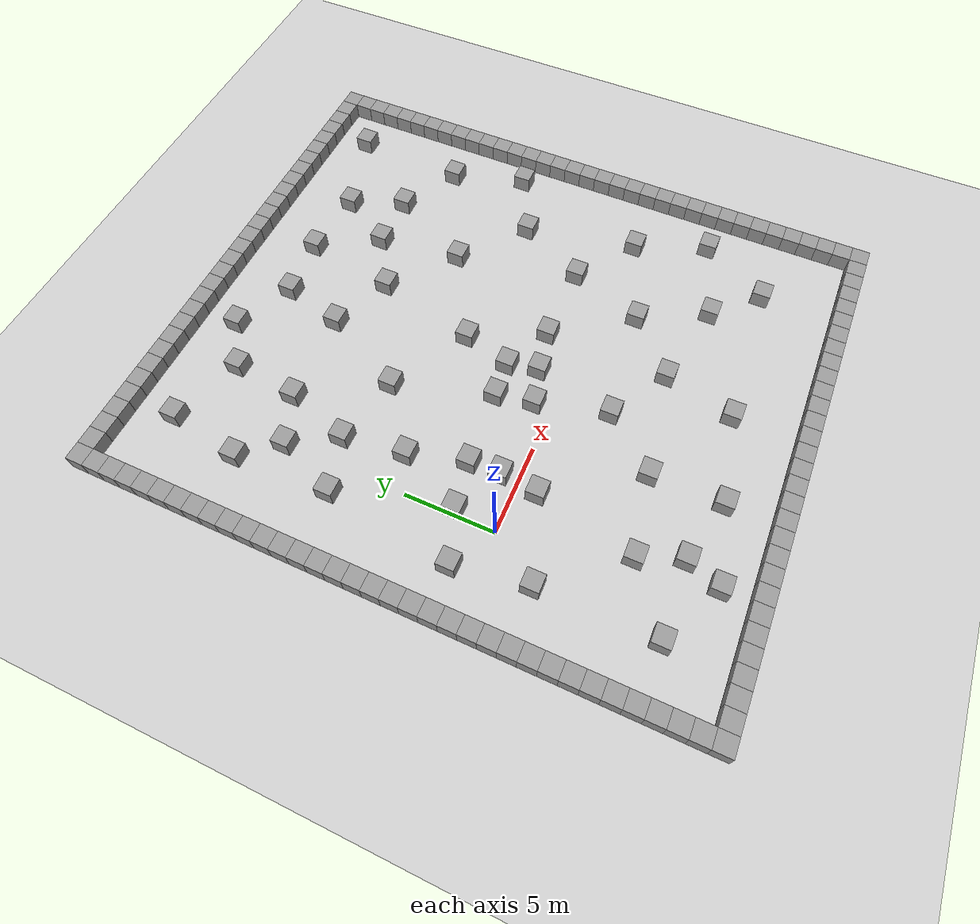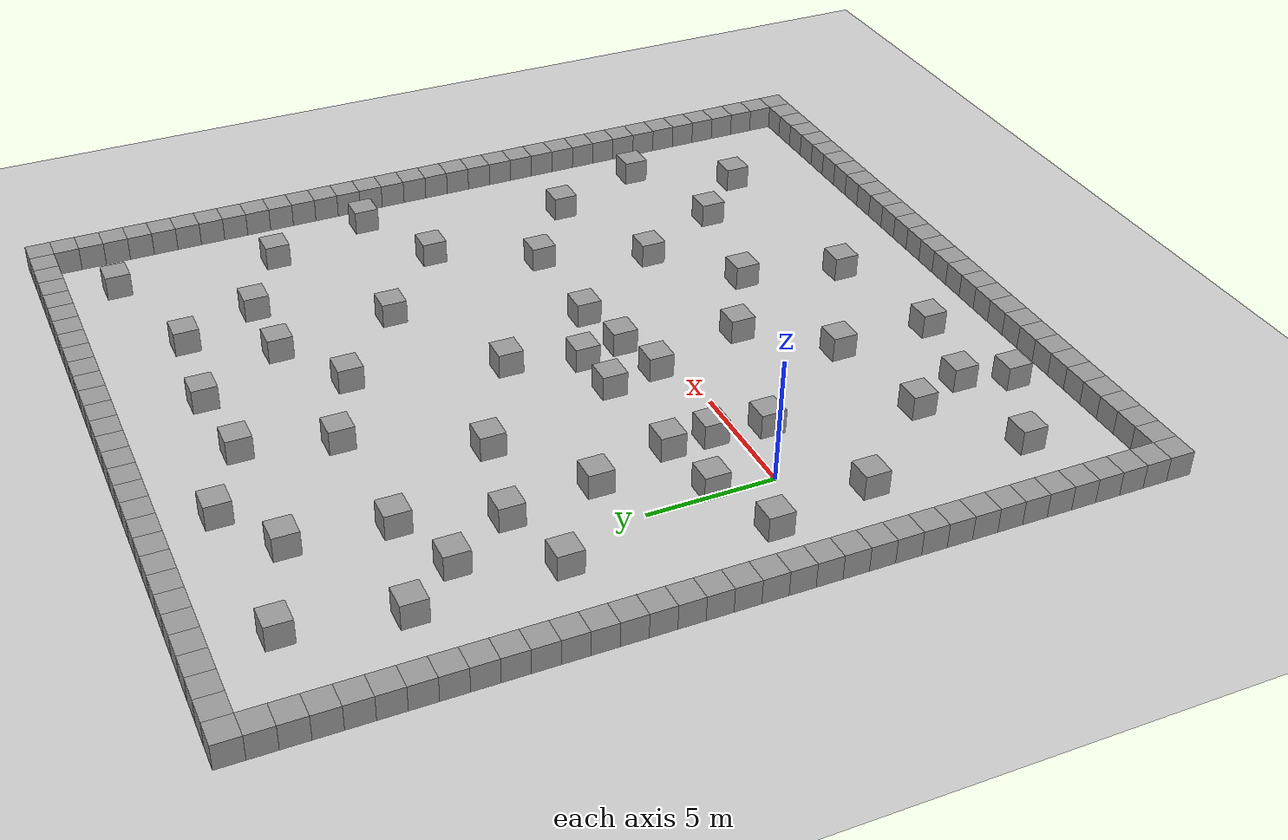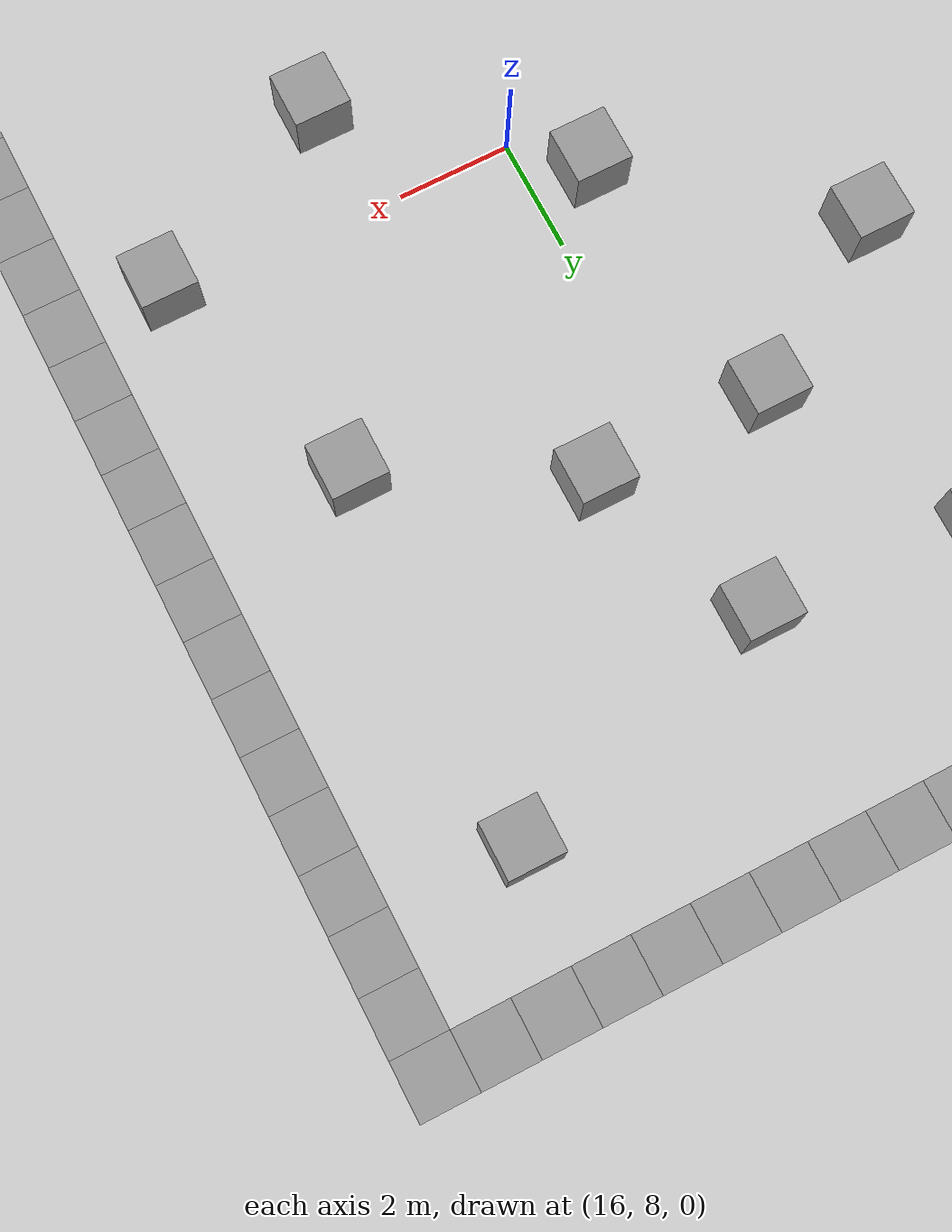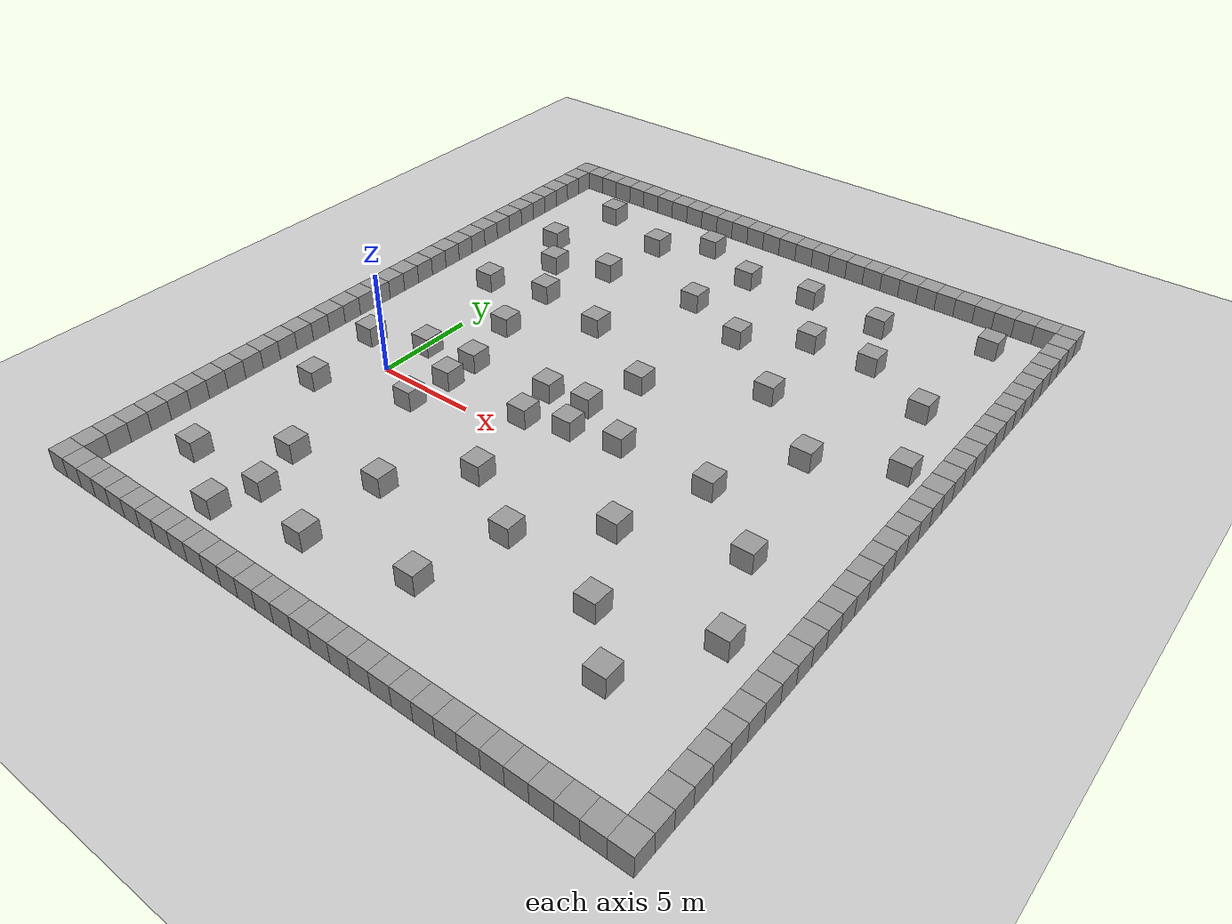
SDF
<sdf version="1.6">
 <world name="default">
  <plugin name="gazebo_occupancy_map" filename="libgazebo_2Dmap_plugin.so">
   <map_resolution>0.05</map_resolution>
   <map_z>0.5</map_z>
   <map_size_x>100</map_size_x>
   <map_size_y>100</map_size_y>
  </plugin>
  <light name="sun" type="directional">
   <pose>0 0 10 0 0 0</pose>
   <diffuse>0.8 0.8 0.8 1</diffuse>
   <specular>0.2 0.2 0.2 1</specular>
   <attenuation>
    <range>1000</range>
    <constant>0.9</constant>
    <linear>0.01</linear>
    <quadratic>0.001</quadratic>
   </attenuation>
   <direction>-0.5 0.1 -0.9</direction>
  </light>
  <model name="ground_plane">
   <static>1</static>
   <link name="link">
    <collision name="collision">
     <geometry><plane><normal>0 0 1</normal><size>100 100</size></plane></geometry>
     <surface><friction><ode><mu>100</mu><mu2>50</mu2></ode></friction></surface>
    </collision>
    <visual name="visual">
     <cast_shadows>0</cast_shadows>
     <geometry><plane><normal>0 0 1</normal><size>100 100</size></plane></geometry>
     <material>
      <script><uri>file://media/materials/scripts/gazebo.material</uri><name>Gazebo/Grey</name></script>
     </material>
    </visual>
    <velocity_decay><linear>0</linear><angular>0</angular></velocity_decay>
   </link>
  </model>
  <physics name="default_physics" default="0" type="ode">
   <max_step_size>0.001</max_step_size>
   <real_time_factor>1</real_time_factor>
   <real_time_update_rate>1000</real_time_update_rate>
  </physics>
  <scene><ambient>0.4 0.4 0.4 1</ambient><background>0.7 0.7 0.7 1</background><shadows>1</shadows></scene>
  <spherical_coordinates>
   <surface_model>EARTH_WGS84</surface_model>
   <latitude_deg>0</latitude_deg>
   <longitude_deg>0</longitude_deg>
   <elevation>0</elevation>
   <heading_deg>0</heading_deg>
  </spherical_coordinates>
  <model name="unit_box_1">
   <pose>-5 5 0.5 0 0 0</pose>
   <static>1</static>
   <link name="link">
    <inertial>
     <mass>1</mass>
     <inertia><ixx>1</ixx><ixy>0</ixy><ixz>0</ixz><iyy>1</iyy><iyz>0</iyz><izz>1</izz></inertia>
    </inertial>
    <collision name="collision"><geometry><box><size>1 1 1</size></box></geometry></collision>
    <visual name="visual">
     <geometry><box><size>1 1 1</size></box></geometry>
     <material>
      <script><uri>file://media/materials/scripts/gazebo.material</uri><name>Gazebo/Grey</name></script>
     </material>
    </visual>
    <velocity_decay><linear>0</linear><angular>0</angular></velocity_decay>
   </link>
   <static>1</static>
  </model>
  <model name="unit_box_40">
   <pose>-5 4 0.5 0 0 0</pose>
   <static>1</static>
   <link name="link">
    <inertial>
     <mass>1</mass>
     <inertia><ixx>1</ixx><ixy>0</ixy><ixz>0</ixz><iyy>1</iyy><iyz>0</iyz><izz>1</izz></inertia>
    </inertial>
    <collision name="collision"><geometry><box><size>1 1 1</size></box></geometry></collision>
    <visual name="visual">
     <geometry><box><size>1 1 1</size></box></geometry>
     <material>
      <script><uri>file://media/materials/scripts/gazebo.material</uri><name>Gazebo/Grey</name></script>
     </material>
    </visual>
    <velocity_decay><linear>0</linear><angular>0</angular></velocity_decay>
   </link>
   <static>1</static>
  </model>
  <model name="unit_box_41">
   <pose>-5 3 0.5 0 0 0</pose>
   <static>1</static>
   <link name="link">
    <inertial>
     <mass>1</mass>
     <inertia><ixx>1</ixx><ixy>0</ixy><ixz>0</ixz><iyy>1</iyy><iyz>0</iyz><izz>1</izz></inertia>
    </inertial>
    <collision name="collision"><geometry><box><size>1 1 1</size></box></geometry></collision>
    <visual name="visual">
     <geometry><box><size>1 1 1</size></box></geometry>
     <material>
      <script><uri>file://media/materials/scripts/gazebo.material</uri><name>Gazebo/Grey</name></script>
     </material>
    </visual>
    <velocity_decay><linear>0</linear><angular>0</angular></velocity_decay>
   </link>
   <static>1</static>
  </model>
  <model name="unit_box_42">
   <pose>-5 2 0.5 0 0 0</pose>
   <static>1</static>
   <link name="link">
    <inertial>
     <mass>1</mass>
     <inertia><ixx>1</ixx><ixy>0</ixy><ixz>0</ixz><iyy>1</iyy><iyz>0</iyz><izz>1</izz></inertia>
    </inertial>
    <collision name="collision"><geometry><box><size>1 1 1</size></box></geometry></collision>
    <visual name="visual">
     <geometry><box><size>1 1 1</size></box></geometry>
     <material>
      <script><uri>file://media/materials/scripts/gazebo.material</uri><name>Gazebo/Grey</name></script>
     </material>
    </visual>
    <velocity_decay><linear>0</linear><angular>0</angular></velocity_decay>
   </link>
   <static>1</static>
  </model>
  <model name="unit_box_43">
   <pose>-5 1 0.5 0 0 0</pose>
   <static>1</static>
   <link name="link">
    <inertial>
     <mass>1</mass>
     <inertia><ixx>1</ixx><ixy>0</ixy><ixz>0</ixz><iyy>1</iyy><iyz>0</iyz><izz>1</izz></inertia>
    </inertial>
    <collision name="collision"><geometry><box><size>1 1 1</size></box></geometry></collision>
    <visual name="visual">
     <geometry><box><size>1 1 1</size></box></geometry>
     <material>
      <script><uri>file://media/materials/scripts/gazebo.material</uri><name>Gazebo/Grey</name></script>
     </material>
    </visual>
    <velocity_decay><linear>0</linear><angular>0</angular></velocity_decay>
   </link>
   <static>1</static>
  </model>
  <model name="unit_box_44">
   <pose>-5 0 0.5 0 0 0</pose>
   <static>1</static>
   <link name="link">
    <inertial>
     <mass>1</mass>
     <inertia><ixx>1</ixx><ixy>0</ixy><ixz>0</ixz><iyy>1</iyy><iyz>0</iyz><izz>1</izz></inertia>
    </inertial>
    <collision name="collision"><geometry><box><size>1 1 1</size></box></geometry></collision>
    <visual name="visual">
     <geometry><box><size>1 1 1</size></box></geometry>
     <material>
      <script><uri>file://media/materials/scripts/gazebo.material</uri><name>Gazebo/Grey</name></script>
     </material>
    </visual>
    <velocity_decay><linear>0</linear><angular>0</angular></velocity_decay>
   </link>
   <static>1</static>
  </model>
  <model name="unit_box_45">
   <pose>-5 -1 0.5 0 0 0</pose>
   <static>1</static>
   <link name="link">
    <inertial>
     <mass>1</mass>
     <inertia><ixx>1</ixx><ixy>0</ixy><ixz>0</ixz><iyy>1</iyy><iyz>0</iyz><izz>1</izz></inertia>
    </inertial>
    <collision name="collision"><geometry><box><size>1 1 1</size></box></geometry></collision>
    <visual name="visual">
     <geometry><box><size>1 1 1</size></box></geometry>
     <material>
      <script><uri>file://media/materials/scripts/gazebo.material</uri><name>Gazebo/Grey</name></script>
     </material>
    </visual>
    <velocity_decay><linear>0</linear><angular>0</angular></velocity_decay>
   </link>
   <static>1</static>
  </model>
  <model name="unit_box_46">
   <pose>-5 -2 0.5 0 0 0</pose>
   <static>1</static>
   <link name="link">
    <inertial>
     <mass>1</mass>
     <inertia><ixx>1</ixx><ixy>0</ixy><ixz>0</ixz><iyy>1</iyy><iyz>0</iyz><izz>1</izz></inertia>
    </inertial>
    <collision name="collision"><geometry><box><size>1 1 1</size></box></geometry></collision>
    <visual name="visual">
     <geometry><box><size>1 1 1</size></box></geometry>
     <material>
      <script><uri>file://media/materials/scripts/gazebo.material</uri><name>Gazebo/Grey</name></script>
     </material>
    </visual>
    <velocity_decay><linear>0</linear><angular>0</angular></velocity_decay>
   </link>
   <static>1</static>
  </model>
  <model name="unit_box_47">
   <pose>-5 -3 0.5 0 0 0</pose>
   <static>1</static>
   <link name="link">
    <inertial>
     <mass>1</mass>
     <inertia><ixx>1</ixx><ixy>0</ixy><ixz>0</ixz><iyy>1</iyy><iyz>0</iyz><izz>1</izz></inertia>
    </inertial>
    <collision name="collision"><geometry><box><size>1 1 1</size></box></geometry></collision>
    <visual name="visual">
     <geometry><box><size>1 1 1</size></box></geometry>
     <material>
      <script><uri>file://media/materials/scripts/gazebo.material</uri><name>Gazebo/Grey</name></script>
     </material>
    </visual>
    <velocity_decay><linear>0</linear><angular>0</angular></velocity_decay>
   </link>
   <static>1</static>
  </model>
  <model name="unit_box_61">
   <pose>-5 6 0.5 0 0 0</pose>
   <static>1</static>
   <link name="link">
    <inertial>
     <mass>1</mass>
     <inertia><ixx>1</ixx><ixy>0</ixy><ixz>0</ixz><iyy>1</iyy><iyz>0</iyz><izz>1</izz></inertia>
    </inertial>
    <collision name="collision"><geometry><box><size>1 1 1</size></box></geometry></collision>
    <visual name="visual">
     <geometry><box><size>1 1 1</size></box></geometry>
     <material>
      <script><uri>file://media/materials/scripts/gazebo.material</uri><name>Gazebo/Grey</name></script>
     </material>
    </visual>
    <velocity_decay><linear>0</linear><angular>0</angular></velocity_decay>
   </link>
   <static>1</static>
  </model>
  <model name="unit_box_67">
   <pose>-5 7 0.5 0 0 0</pose>
   <static>1</static>
   <link name="link">
    <inertial>
     <mass>1</mass>
     <inertia><ixx>1</ixx><ixy>0</ixy><ixz>0</ixz><iyy>1</iyy><iyz>0</iyz><izz>1</izz></inertia>
    </inertial>
    <collision name="collision"><geometry><box><size>1 1 1</size></box></geometry></collision>
    <visual name="visual">
     <geometry><box><size>1 1 1</size></box></geometry>
     <material>
      <script><uri>file://media/materials/scripts/gazebo.material</uri><name>Gazebo/Grey</name></script>
     </material>
    </visual>
    <velocity_decay><linear>0</linear><angular>0</angular></velocity_decay>
   </link>
   <static>1</static>
  </model>
  <model name="unit_box_68">
   <pose>-5 8 0.5 0 0 0</pose>
   <static>1</static>
   <link name="link">
    <inertial>
     <mass>1</mass>
     <inertia><ixx>1</ixx><ixy>0</ixy><ixz>0</ixz><iyy>1</iyy><iyz>0</iyz><izz>1</izz></inertia>
    </inertial>
    <collision name="collision"><geometry><box><size>1 1 1</size></box></geometry></collision>
    <visual name="visual">
     <geometry><box><size>1 1 1</size></box></geometry>
     <material>
      <script><uri>file://media/materials/scripts/gazebo.material</uri><name>Gazebo/Grey</name></script>
     </material>
    </visual>
    <velocity_decay><linear>0</linear><angular>0</angular></velocity_decay>
   </link>
   <static>1</static>
  </model>
  <model name="unit_box_69">
   <pose>-5 9 0.5 0 0 0</pose>
   <static>1</static>
   <link name="link">
    <inertial>
     <mass>1</mass>
     <inertia><ixx>1</ixx><ixy>0</ixy><ixz>0</ixz><iyy>1</iyy><iyz>0</iyz><izz>1</izz></inertia>
    </inertial>
    <collision name="collision"><geometry><box><size>1 1 1</size></box></geometry></collision>
    <visual name="visual">
     <geometry><box><size>1 1 1</size></box></geometry>
     <material>
      <script><uri>file://media/materials/scripts/gazebo.material</uri><name>Gazebo/Grey</name></script>
     </material>
    </visual>
    <velocity_decay><linear>0</linear><angular>0</angular></velocity_decay>
   </link>
   <static>1</static>
  </model>
  <model name="unit_box_72">
   <pose>-5 10 0.5 0 0 0</pose>
   <static>1</static>
   <link name="link">
    <inertial>
     <mass>1</mass>
     <inertia><ixx>1</ixx><ixy>0</ixy><ixz>0</ixz><iyy>1</iyy><iyz>0</iyz><izz>1</izz></inertia>
    </inertial>
    <collision name="collision"><geometry><box><size>1 1 1</size></box></geometry></collision>
    <visual name="visual">
     <geometry><box><size>1 1 1</size></box></geometry>
     <material>
      <script><uri>file://media/materials/scripts/gazebo.material</uri><name>Gazebo/Grey</name></script>
     </material>
    </visual>
    <velocity_decay><linear>0</linear><angular>0</angular></velocity_decay>
   </link>
   <static>1</static>
  </model>
  <model name="unit_box_73">
   <pose>-5 11 0.5 0 0 0</pose>
   <static>1</static>
   <link name="link">
    <inertial>
     <mass>1</mass>
     <inertia><ixx>1</ixx><ixy>0</ixy><ixz>0</ixz><iyy>1</iyy><iyz>0</iyz><izz>1</izz></inertia>
    </inertial>
    <collision name="collision"><geometry><box><size>1 1 1</size></box></geometry></collision>
    <visual name="visual">
     <geometry><box><size>1 1 1</size></box></geometry>
     <material>
      <script><uri>file://media/materials/scripts/gazebo.material</uri><name>Gazebo/Grey</name></script>
     </material>
    </visual>
    <velocity_decay><linear>0</linear><angular>0</angular></velocity_decay>
   </link>
   <static>1</static>
  </model>
  <model name="unit_box_74">
   <pose>-5 12 0.5 0 0 0</pose>
   <static>1</static>
   <link name="link">
    <inertial>
     <mass>1</mass>
     <inertia><ixx>1</ixx><ixy>0</ixy><ixz>0</ixz><iyy>1</iyy><iyz>0</iyz><izz>1</izz></inertia>
    </inertial>
    <collision name="collision"><geometry><box><size>1 1 1</size></box></geometry></collision>
    <visual name="visual">
     <geometry><box><size>1 1 1</size></box></geometry>
     <material>
      <script><uri>file://media/materials/scripts/gazebo.material</uri><name>Gazebo/Grey</name></script>
     </material>
    </visual>
    <velocity_decay><linear>0</linear><angular>0</angular></velocity_decay>
   </link>
   <static>1</static>
  </model>
  <model name="unit_box_75">
   <pose>-5 13 0.5 0 0 0</pose>
   <static>1</static>
   <link name="link">
    <inertial>
     <mass>1</mass>
     <inertia><ixx>1</ixx><ixy>0</ixy><ixz>0</ixz><iyy>1</iyy><iyz>0</iyz><izz>1</izz></inertia>
    </inertial>
    <collision name="collision"><geometry><box><size>1 1 1</size></box></geometry></collision>
    <visual name="visual">
     <geometry><box><size>1 1 1</size></box></geometry>
     <material>
      <script><uri>file://media/materials/scripts/gazebo.material</uri><name>Gazebo/Grey</name></script>
     </material>
    </visual>
    <velocity_decay><linear>0</linear><angular>0</angular></velocity_decay>
   </link>
   <static>1</static>
  </model>
  <model name="unit_box_76">
   <pose>-5 14 0.5 0 0 0</pose>
   <static>1</static>
   <link name="link">
    <inertial>
     <mass>1</mass>
     <inertia><ixx>1</ixx><ixy>0</ixy><ixz>0</ixz><iyy>1</iyy><iyz>0</iyz><izz>1</izz></inertia>
    </inertial>
    <collision name="collision"><geometry><box><size>1 1 1</size></box></geometry></collision>
    <visual name="visual">
     <geometry><box><size>1 1 1</size></box></geometry>
     <material>
      <script><uri>file://media/materials/scripts/gazebo.material</uri><name>Gazebo/Grey</name></script>
     </material>
    </visual>
    <velocity_decay><linear>0</linear><angular>0</angular></velocity_decay>
   </link>
   <static>1</static>
  </model>
  <model name="unit_box_77">
   <pose>-5 15 0.5 0 0 0</pose>
   <static>1</static>
   <link name="link">
    <inertial>
     <mass>1</mass>
     <inertia><ixx>1</ixx><ixy>0</ixy><ixz>0</ixz><iyy>1</iyy><iyz>0</iyz><izz>1</izz></inertia>
    </inertial>
    <collision name="collision"><geometry><box><size>1 1 1</size></box></geometry></collision>
    <visual name="visual">
     <geometry><box><size>1 1 1</size></box></geometry>
     <material>
      <script><uri>file://media/materials/scripts/gazebo.material</uri><name>Gazebo/Grey</name></script>
     </material>
    </visual>
    <velocity_decay><linear>0</linear><angular>0</angular></velocity_decay>
   </link>
   <static>1</static>
  </model>
  <model name="unit_box_78">
   <pose>-5 16 0.5 0 0 0</pose>
   <static>1</static>
   <link name="link">
    <inertial>
     <mass>1</mass>
     <inertia><ixx>1</ixx><ixy>0</ixy><ixz>0</ixz><iyy>1</iyy><iyz>0</iyz><izz>1</izz></inertia>
    </inertial>
    <collision name="collision"><geometry><box><size>1 1 1</size></box></geometry></collision>
    <visual name="visual">
     <geometry><box><size>1 1 1</size></box></geometry>
     <material>
      <script><uri>file://media/materials/scripts/gazebo.material</uri><name>Gazebo/Grey</name></script>
     </material>
    </visual>
    <velocity_decay><linear>0</linear><angular>0</angular></velocity_decay>
   </link>
   <static>1</static>
  </model>
  <model name="unit_box_79">
   <pose>-5 17 0.5 0 0 0</pose>
   <static>1</static>
   <link name="link">
    <inertial>
     <mass>1</mass>
     <inertia><ixx>1</ixx><ixy>0</ixy><ixz>0</ixz><iyy>1</iyy><iyz>0</iyz><izz>1</izz></inertia>
    </inertial>
    <collision name="collision"><geometry><box><size>1 1 1</size></box></geometry></collision>
    <visual name="visual">
     <geometry><box><size>1 1 1</size></box></geometry>
     <material>
      <script><uri>file://media/materials/scripts/gazebo.material</uri><name>Gazebo/Grey</name></script>
     </material>
    </visual>
    <velocity_decay><linear>0</linear><angular>0</angular></velocity_decay>
   </link>
   <static>1</static>
  </model>
  <model name="unit_box_80">
   <pose>-5 18 0.5 0 0 0</pose>
   <static>1</static>
   <link name="link">
    <inertial>
     <mass>1</mass>
     <inertia><ixx>1</ixx><ixy>0</ixy><ixz>0</ixz><iyy>1</iyy><iyz>0</iyz><izz>1</izz></inertia>
    </inertial>
    <collision name="collision"><geometry><box><size>1 1 1</size></box></geometry></collision>
    <visual name="visual">
     <geometry><box><size>1 1 1</size></box></geometry>
     <material>
      <script><uri>file://media/materials/scripts/gazebo.material</uri><name>Gazebo/Grey</name></script>
     </material>
    </visual>
    <velocity_decay><linear>0</linear><angular>0</angular></velocity_decay>
   </link>
   <static>1</static>
  </model>
  <model name="unit_box_96">
   <pose>-5 19 0.5 0 0 0</pose>
   <static>1</static>
   <link name="link">
    <inertial>
     <mass>1</mass>
     <inertia><ixx>1</ixx><ixy>0</ixy><ixz>0</ixz><iyy>1</iyy><iyz>0</iyz><izz>1</izz></inertia>
    </inertial>
    <collision name="collision"><geometry><box><size>1 1 1</size></box></geometry></collision>
    <visual name="visual">
     <geometry><box><size>1 1 1</size></box></geometry>
     <material>
      <script><uri>file://media/materials/scripts/gazebo.material</uri><name>Gazebo/Grey</name></script>
     </material>
    </visual>
    <velocity_decay><linear>0</linear><angular>0</angular></velocity_decay>
   </link>
   <static>1</static>
  </model>
  <model name="unit_box_97">
   <pose>-5 20 0.5 0 0 0</pose>
   <static>1</static>
   <link name="link">
    <inertial>
     <mass>1</mass>
     <inertia><ixx>1</ixx><ixy>0</ixy><ixz>0</ixz><iyy>1</iyy><iyz>0</iyz><izz>1</izz></inertia>
    </inertial>
    <collision name="collision"><geometry><box><size>1 1 1</size></box></geometry></collision>
    <visual name="visual">
     <geometry><box><size>1 1 1</size></box></geometry>
     <material>
      <script><uri>file://media/materials/scripts/gazebo.material</uri><name>Gazebo/Grey</name></script>
     </material>
    </visual>
    <velocity_decay><linear>0</linear><angular>0</angular></velocity_decay>
   </link>
   <static>1</static>
  </model>
  <model name="unit_box_98">
   <pose>-5 21 0.5 0 0 0</pose>
   <static>1</static>
   <link name="link">
    <inertial>
     <mass>1</mass>
     <inertia><ixx>1</ixx><ixy>0</ixy><ixz>0</ixz><iyy>1</iyy><iyz>0</iyz><izz>1</izz></inertia>
    </inertial>
    <collision name="collision"><geometry><box><size>1 1 1</size></box></geometry></collision>
    <visual name="visual">
     <geometry><box><size>1 1 1</size></box></geometry>
     <material>
      <script><uri>file://media/materials/scripts/gazebo.material</uri><name>Gazebo/Grey</name></script>
     </material>
    </visual>
    <velocity_decay><linear>0</linear><angular>0</angular></velocity_decay>
   </link>
   <static>1</static>
  </model>
  <model name="unit_box_99">
   <pose>-4 21 0.5 0 0 0</pose>
   <static>1</static>
   <link name="link">
    <inertial>
     <mass>1</mass>
     <inertia><ixx>1</ixx><ixy>0</ixy><ixz>0</ixz><iyy>1</iyy><iyz>0</iyz><izz>1</izz></inertia>
    </inertial>
    <collision name="collision"><geometry><box><size>1 1 1</size></box></geometry></collision>
    <visual name="visual">
     <geometry><box><size>1 1 1</size></box></geometry>
     <material>
      <script><uri>file://media/materials/scripts/gazebo.material</uri><name>Gazebo/Grey</name></script>
     </material>
    </visual>
    <velocity_decay><linear>0</linear><angular>0</angular></velocity_decay>
   </link>
   <static>1</static>
  </model>
  <model name="unit_box_100">
   <pose>-3 21 0.5 0 0 0</pose>
   <static>1</static>
   <link name="link">
    <inertial>
     <mass>1</mass>
     <inertia><ixx>1</ixx><ixy>0</ixy><ixz>0</ixz><iyy>1</iyy><iyz>0</iyz><izz>1</izz></inertia>
    </inertial>
    <collision name="collision"><geometry><box><size>1 1 1</size></box></geometry></collision>
    <visual name="visual">
     <geometry><box><size>1 1 1</size></box></geometry>
     <material>
      <script><uri>file://media/materials/scripts/gazebo.material</uri><name>Gazebo/Grey</name></script>
     </material>
    </visual>
    <velocity_decay><linear>0</linear><angular>0</angular></velocity_decay>
   </link>
   <static>1</static>
  </model>
  <model name="unit_box_101">
   <pose>-2 21 0.5 0 0 0</pose>
   <static>1</static>
   <link name="link">
    <inertial>
     <mass>1</mass>
     <inertia><ixx>1</ixx><ixy>0</ixy><ixz>0</ixz><iyy>1</iyy><iyz>0</iyz><izz>1</izz></inertia>
    </inertial>
    <collision name="collision"><geometry><box><size>1 1 1</size></box></geometry></collision>
    <visual name="visual">
     <geometry><box><size>1 1 1</size></box></geometry>
     <material>
      <script><uri>file://media/materials/scripts/gazebo.material</uri><name>Gazebo/Grey</name></script>
     </material>
    </visual>
    <velocity_decay><linear>0</linear><angular>0</angular></velocity_decay>
   </link>
   <static>1</static>
  </model>
  <model name="unit_box_102">
   <pose>-1 21 0.5 0 0 0</pose>
   <static>1</static>
   <link name="link">
    <inertial>
     <mass>1</mass>
     <inertia><ixx>1</ixx><ixy>0</ixy><ixz>0</ixz><iyy>1</iyy><iyz>0</iyz><izz>1</izz></inertia>
    </inertial>
    <collision name="collision"><geometry><box><size>1 1 1</size></box></geometry></collision>
    <visual name="visual">
     <geometry><box><size>1 1 1</size></box></geometry>
     <material>
      <script><uri>file://media/materials/scripts/gazebo.material</uri><name>Gazebo/Grey</name></script>
     </material>
    </visual>
    <velocity_decay><linear>0</linear><angular>0</angular></velocity_decay>
   </link>
   <static>1</static>
  </model>
  <model name="unit_box_103">
   <pose>0 21 0.5 0 0 0</pose>
   <static>1</static>
   <link name="link">
    <inertial>
     <mass>1</mass>
     <inertia><ixx>1</ixx><ixy>0</ixy><ixz>0</ixz><iyy>1</iyy><iyz>0</iyz><izz>1</izz></inertia>
    </inertial>
    <collision name="collision"><geometry><box><size>1 1 1</size></box></geometry></collision>
    <visual name="visual">
     <geometry><box><size>1 1 1</size></box></geometry>
     <material>
      <script><uri>file://media/materials/scripts/gazebo.material</uri><name>Gazebo/Grey</name></script>
     </material>
    </visual>
    <velocity_decay><linear>0</linear><angular>0</angular></velocity_decay>
   </link>
   <static>1</static>
  </model>
  <model name="unit_box_104">
   <pose>1 21 0.5 0 0 0</pose>
   <static>1</static>
   <link name="link">
    <inertial>
     <mass>1</mass>
     <inertia><ixx>1</ixx><ixy>0</ixy><ixz>0</ixz><iyy>1</iyy><iyz>0</iyz><izz>1</izz></inertia>
    </inertial>
    <collision name="collision"><geometry><box><size>1 1 1</size></box></geometry></collision>
    <visual name="visual">
     <geometry><box><size>1 1 1</size></box></geometry>
     <material>
      <script><uri>file://media/materials/scripts/gazebo.material</uri><name>Gazebo/Grey</name></script>
     </material>
    </visual>
    <velocity_decay><linear>0</linear><angular>0</angular></velocity_decay>
   </link>
   <static>1</static>
  </model>
  <model name="unit_box_105">
   <pose>2 21 0.5 0 0 0</pose>
   <static>1</static>
   <link name="link">
    <inertial>
     <mass>1</mass>
     <inertia><ixx>1</ixx><ixy>0</ixy><ixz>0</ixz><iyy>1</iyy><iyz>0</iyz><izz>1</izz></inertia>
    </inertial>
    <collision name="collision"><geometry><box><size>1 1 1</size></box></geometry></collision>
    <visual name="visual">
     <geometry><box><size>1 1 1</size></box></geometry>
     <material>
      <script><uri>file://media/materials/scripts/gazebo.material</uri><name>Gazebo/Grey</name></script>
     </material>
    </visual>
    <velocity_decay><linear>0</linear><angular>0</angular></velocity_decay>
   </link>
   <static>1</static>
  </model>
  <model name="unit_box_106">
   <pose>3 21 0.5 0 0 0</pose>
   <static>1</static>
   <link name="link">
    <inertial>
     <mass>1</mass>
     <inertia><ixx>1</ixx><ixy>0</ixy><ixz>0</ixz><iyy>1</iyy><iyz>0</iyz><izz>1</izz></inertia>
    </inertial>
    <collision name="collision"><geometry><box><size>1 1 1</size></box></geometry></collision>
    <visual name="visual">
     <geometry><box><size>1 1 1</size></box></geometry>
     <material>
      <script><uri>file://media/materials/scripts/gazebo.material</uri><name>Gazebo/Grey</name></script>
     </material>
    </visual>
    <velocity_decay><linear>0</linear><angular>0</angular></velocity_decay>
   </link>
   <static>1</static>
  </model>
  <model name="unit_box_107">
   <pose>4 21 0.5 0 0 0</pose>
   <static>1</static>
   <link name="link">
    <inertial>
     <mass>1</mass>
     <inertia><ixx>1</ixx><ixy>0</ixy><ixz>0</ixz><iyy>1</iyy><iyz>0</iyz><izz>1</izz></inertia>
    </inertial>
    <collision name="collision"><geometry><box><size>1 1 1</size></box></geometry></collision>
    <visual name="visual">
     <geometry><box><size>1 1 1</size></box></geometry>
     <material>
      <script><uri>file://media/materials/scripts/gazebo.material</uri><name>Gazebo/Grey</name></script>
     </material>
    </visual>
    <velocity_decay><linear>0</linear><angular>0</angular></velocity_decay>
   </link>
   <static>1</static>
  </model>
  <model name="unit_box_108">
   <pose>5 21 0.5 0 0 0</pose>
   <static>1</static>
   <link name="link">
    <inertial>
     <mass>1</mass>
     <inertia><ixx>1</ixx><ixy>0</ixy><ixz>0</ixz><iyy>1</iyy><iyz>0</iyz><izz>1</izz></inertia>
    </inertial>
    <collision name="collision"><geometry><box><size>1 1 1</size></box></geometry></collision>
    <visual name="visual">
     <geometry><box><size>1 1 1</size></box></geometry>
     <material>
      <script><uri>file://media/materials/scripts/gazebo.material</uri><name>Gazebo/Grey</name></script>
     </material>
    </visual>
    <velocity_decay><linear>0</linear><angular>0</angular></velocity_decay>
   </link>
   <static>1</static>
  </model>
  <model name="unit_box_109">
   <pose>6 21 0.5 0 0 0</pose>
   <static>1</static>
   <link name="link">
    <inertial>
     <mass>1</mass>
     <inertia><ixx>1</ixx><ixy>0</ixy><ixz>0</ixz><iyy>1</iyy><iyz>0</iyz><izz>1</izz></inertia>
    </inertial>
    <collision name="collision"><geometry><box><size>1 1 1</size></box></geometry></collision>
    <visual name="visual">
     <geometry><box><size>1 1 1</size></box></geometry>
     <material>
      <script><uri>file://media/materials/scripts/gazebo.material</uri><name>Gazebo/Grey</name></script>
     </material>
    </visual>
    <velocity_decay><linear>0</linear><angular>0</angular></velocity_decay>
   </link>
   <static>1</static>
  </model>
  <model name="unit_box_110">
   <pose>7 21 0.5 0 0 0</pose>
   <static>1</static>
   <link name="link">
    <inertial>
     <mass>1</mass>
     <inertia><ixx>1</ixx><ixy>0</ixy><ixz>0</ixz><iyy>1</iyy><iyz>0</iyz><izz>1</izz></inertia>
    </inertial>
    <collision name="collision"><geometry><box><size>1 1 1</size></box></geometry></collision>
    <visual name="visual">
     <geometry><box><size>1 1 1</size></box></geometry>
     <material>
      <script><uri>file://media/materials/scripts/gazebo.material</uri><name>Gazebo/Grey</name></script>
     </material>
    </visual>
    <velocity_decay><linear>0</linear><angular>0</angular></velocity_decay>
   </link>
   <static>1</static>
  </model>
  <model name="unit_box_111">
   <pose>8 21 0.5 0 0 0</pose>
   <static>1</static>
   <link name="link">
    <inertial>
     <mass>1</mass>
     <inertia><ixx>1</ixx><ixy>0</ixy><ixz>0</ixz><iyy>1</iyy><iyz>0</iyz><izz>1</izz></inertia>
    </inertial>
    <collision name="collision"><geometry><box><size>1 1 1</size></box></geometry></collision>
    <visual name="visual">
     <geometry><box><size>1 1 1</size></box></geometry>
     <material>
      <script><uri>file://media/materials/scripts/gazebo.material</uri><name>Gazebo/Grey</name></script>
     </material>
    </visual>
    <velocity_decay><linear>0</linear><angular>0</angular></velocity_decay>
   </link>
   <static>1</static>
  </model>
  <model name="unit_box_112">
   <pose>9 21 0.5 0 0 0</pose>
   <static>1</static>
   <link name="link">
    <inertial>
     <mass>1</mass>
     <inertia><ixx>1</ixx><ixy>0</ixy><ixz>0</ixz><iyy>1</iyy><iyz>0</iyz><izz>1</izz></inertia>
    </inertial>
    <collision name="collision"><geometry><box><size>1 1 1</size></box></geometry></collision>
    <visual name="visual">
     <geometry><box><size>1 1 1</size></box></geometry>
     <material>
      <script><uri>file://media/materials/scripts/gazebo.material</uri><name>Gazebo/Grey</name></script>
     </material>
    </visual>
    <velocity_decay><linear>0</linear><angular>0</angular></velocity_decay>
   </link>
   <static>1</static>
  </model>
  <model name="unit_box_113">
   <pose>10 21 0.5 0 0 0</pose>
   <static>1</static>
   <link name="link">
    <inertial>
     <mass>1</mass>
     <inertia><ixx>1</ixx><ixy>0</ixy><ixz>0</ixz><iyy>1</iyy><iyz>0</iyz><izz>1</izz></inertia>
    </inertial>
    <collision name="collision"><geometry><box><size>1 1 1</size></box></geometry></collision>
    <visual name="visual">
     <geometry><box><size>1 1 1</size></box></geometry>
     <material>
      <script><uri>file://media/materials/scripts/gazebo.material</uri><name>Gazebo/Grey</name></script>
     </material>
    </visual>
    <velocity_decay><linear>0</linear><angular>0</angular></velocity_decay>
   </link>
   <static>1</static>
  </model>
  <model name="unit_box_114">
   <pose>11 21 0.5 0 0 0</pose>
   <static>1</static>
   <link name="link">
    <inertial>
     <mass>1</mass>
     <inertia><ixx>1</ixx><ixy>0</ixy><ixz>0</ixz><iyy>1</iyy><iyz>0</iyz><izz>1</izz></inertia>
    </inertial>
    <collision name="collision"><geometry><box><size>1 1 1</size></box></geometry></collision>
    <visual name="visual">
     <geometry><box><size>1 1 1</size></box></geometry>
     <material>
      <script><uri>file://media/materials/scripts/gazebo.material</uri><name>Gazebo/Grey</name></script>
     </material>
    </visual>
    <velocity_decay><linear>0</linear><angular>0</angular></velocity_decay>
   </link>
   <static>1</static>
  </model>
  <model name="unit_box_115">
   <pose>12 21 0.5 0 0 0</pose>
   <static>1</static>
   <link name="link">
    <inertial>
     <mass>1</mass>
     <inertia><ixx>1</ixx><ixy>0</ixy><ixz>0</ixz><iyy>1</iyy><iyz>0</iyz><izz>1</izz></inertia>
    </inertial>
    <collision name="collision"><geometry><box><size>1 1 1</size></box></geometry></collision>
    <visual name="visual">
     <geometry><box><size>1 1 1</size></box></geometry>
     <material>
      <script><uri>file://media/materials/scripts/gazebo.material</uri><name>Gazebo/Grey</name></script>
     </material>
    </visual>
    <velocity_decay><linear>0</linear><angular>0</angular></velocity_decay>
   </link>
   <static>1</static>
  </model>
  <model name="unit_box_116">
   <pose>13 21 0.5 0 0 0</pose>
   <static>1</static>
   <link name="link">
    <inertial>
     <mass>1</mass>
     <inertia><ixx>1</ixx><ixy>0</ixy><ixz>0</ixz><iyy>1</iyy><iyz>0</iyz><izz>1</izz></inertia>
    </inertial>
    <collision name="collision"><geometry><box><size>1 1 1</size></box></geometry></collision>
    <visual name="visual">
     <geometry><box><size>1 1 1</size></box></geometry>
     <material>
      <script><uri>file://media/materials/scripts/gazebo.material</uri><name>Gazebo/Grey</name></script>
     </material>
    </visual>
    <velocity_decay><linear>0</linear><angular>0</angular></velocity_decay>
   </link>
   <static>1</static>
  </model>
  <model name="unit_box_121">
   <pose>14 21 0.5 0 0 0</pose>
   <static>1</static>
   <link name="link">
    <inertial>
     <mass>1</mass>
     <inertia><ixx>1</ixx><ixy>0</ixy><ixz>0</ixz><iyy>1</iyy><iyz>0</iyz><izz>1</izz></inertia>
    </inertial>
    <collision name="collision"><geometry><box><size>1 1 1</size></box></geometry></collision>
    <visual name="visual">
     <geometry><box><size>1 1 1</size></box></geometry>
     <material>
      <script><uri>file://media/materials/scripts/gazebo.material</uri><name>Gazebo/Grey</name></script>
     </material>
    </visual>
    <velocity_decay><linear>0</linear><angular>0</angular></velocity_decay>
   </link>
   <static>1</static>
  </model>
  <model name="unit_box_134">
   <pose>15 21 0.5 0 0 0</pose>
   <static>1</static>
   <link name="link">
    <inertial>
     <mass>1</mass>
     <inertia><ixx>1</ixx><ixy>0</ixy><ixz>0</ixz><iyy>1</iyy><iyz>0</iyz><izz>1</izz></inertia>
    </inertial>
    <collision name="collision"><geometry><box><size>1 1 1</size></box></geometry></collision>
    <visual name="visual">
     <geometry><box><size>1 1 1</size></box></geometry>
     <material>
      <script><uri>file://media/materials/scripts/gazebo.material</uri><name>Gazebo/Grey</name></script>
     </material>
    </visual>
    <velocity_decay><linear>0</linear><angular>0</angular></velocity_decay>
   </link>
   <static>1</static>
  </model>
  <model name="unit_box_135">
   <pose>16 21 0.5 0 0 0</pose>
   <static>1</static>
   <link name="link">
    <inertial>
     <mass>1</mass>
     <inertia><ixx>1</ixx><ixy>0</ixy><ixz>0</ixz><iyy>1</iyy><iyz>0</iyz><izz>1</izz></inertia>
    </inertial>
    <collision name="collision"><geometry><box><size>1 1 1</size></box></geometry></collision>
    <visual name="visual">
     <geometry><box><size>1 1 1</size></box></geometry>
     <material>
      <script><uri>file://media/materials/scripts/gazebo.material</uri><name>Gazebo/Grey</name></script>
     </material>
    </visual>
    <velocity_decay><linear>0</linear><angular>0</angular></velocity_decay>
   </link>
   <static>1</static>
  </model>
  <model name="unit_box_136">
   <pose>17 21 0.5 0 0 0</pose>
   <static>1</static>
   <link name="link">
    <inertial>
     <mass>1</mass>
     <inertia><ixx>1</ixx><ixy>0</ixy><ixz>0</ixz><iyy>1</iyy><iyz>0</iyz><izz>1</izz></inertia>
    </inertial>
    <collision name="collision"><geometry><box><size>1 1 1</size></box></geometry></collision>
    <visual name="visual">
     <geometry><box><size>1 1 1</size></box></geometry>
     <material>
      <script><uri>file://media/materials/scripts/gazebo.material</uri><name>Gazebo/Grey</name></script>
     </material>
    </visual>
    <velocity_decay><linear>0</linear><angular>0</angular></velocity_decay>
   </link>
   <static>1</static>
  </model>
  <model name="unit_box_137">
   <pose>18 21 0.5 0 0 0</pose>
   <static>1</static>
   <link name="link">
    <inertial>
     <mass>1</mass>
     <inertia><ixx>1</ixx><ixy>0</ixy><ixz>0</ixz><iyy>1</iyy><iyz>0</iyz><izz>1</izz></inertia>
    </inertial>
    <collision name="collision"><geometry><box><size>1 1 1</size></box></geometry></collision>
    <visual name="visual">
     <geometry><box><size>1 1 1</size></box></geometry>
     <material>
      <script><uri>file://media/materials/scripts/gazebo.material</uri><name>Gazebo/Grey</name></script>
     </material>
    </visual>
    <velocity_decay><linear>0</linear><angular>0</angular></velocity_decay>
   </link>
   <static>1</static>
  </model>
  <model name="unit_box_146">
   <pose>19 21 0.5 0 0 0</pose>
   <static>1</static>
   <link name="link">
    <inertial>
     <mass>1</mass>
     <inertia><ixx>1</ixx><ixy>0</ixy><ixz>0</ixz><iyy>1</iyy><iyz>0</iyz><izz>1</izz></inertia>
    </inertial>
    <collision name="collision"><geometry><box><size>1 1 1</size></box></geometry></collision>
    <visual name="visual">
     <geometry><box><size>1 1 1</size></box></geometry>
     <material>
      <script><uri>file://media/materials/scripts/gazebo.material</uri><name>Gazebo/Grey</name></script>
     </material>
    </visual>
    <velocity_decay><linear>0</linear><angular>0</angular></velocity_decay>
   </link>
   <static>1</static>
  </model>
  <model name="unit_box_147">
   <pose>20 21 0.5 0 0 0</pose>
   <static>1</static>
   <link name="link">
    <inertial>
     <mass>1</mass>
     <inertia><ixx>1</ixx><ixy>0</ixy><ixz>0</ixz><iyy>1</iyy><iyz>0</iyz><izz>1</izz></inertia>
    </inertial>
    <collision name="collision"><geometry><box><size>1 1 1</size></box></geometry></collision>
    <visual name="visual">
     <geometry><box><size>1 1 1</size></box></geometry>
     <material>
      <script><uri>file://media/materials/scripts/gazebo.material</uri><name>Gazebo/Grey</name></script>
     </material>
    </visual>
    <velocity_decay><linear>0</linear><angular>0</angular></velocity_decay>
   </link>
   <static>1</static>
  </model>
  <model name="unit_box_148">
   <pose>21 21 0.5 0 0 0</pose>
   <static>1</static>
   <link name="link">
    <inertial>
     <mass>1</mass>
     <inertia><ixx>1</ixx><ixy>0</ixy><ixz>0</ixz><iyy>1</iyy><iyz>0</iyz><izz>1</izz></inertia>
    </inertial>
    <collision name="collision"><geometry><box><size>1 1 1</size></box></geometry></collision>
    <visual name="visual">
     <geometry><box><size>1 1 1</size></box></geometry>
     <material>
      <script><uri>file://media/materials/scripts/gazebo.material</uri><name>Gazebo/Grey</name></script>
     </material>
    </visual>
    <velocity_decay><linear>0</linear><angular>0</angular></velocity_decay>
   </link>
   <static>1</static>
  </model>
  <model name="unit_box_150">
   <pose>22 21 0.5 0 0 0</pose>
   <static>1</static>
   <link name="link">
    <inertial>
     <mass>1</mass>
     <inertia><ixx>1</ixx><ixy>0</ixy><ixz>0</ixz><iyy>1</iyy><iyz>0</iyz><izz>1</izz></inertia>
    </inertial>
    <collision name="collision"><geometry><box><size>1 1 1</size></box></geometry></collision>
    <visual name="visual">
     <geometry><box><size>1 1 1</size></box></geometry>
     <material>
      <script><uri>file://media/materials/scripts/gazebo.material</uri><name>Gazebo/Grey</name></script>
     </material>
    </visual>
    <velocity_decay><linear>0</linear><angular>0</angular></velocity_decay>
   </link>
   <static>1</static>
  </model>
  <model name="unit_box_151">
   <pose>23 21 0.5 0 0 0</pose>
   <static>1</static>
   <link name="link">
    <inertial>
     <mass>1</mass>
     <inertia><ixx>1</ixx><ixy>0</ixy><ixz>0</ixz><iyy>1</iyy><iyz>0</iyz><izz>1</izz></inertia>
    </inertial>
    <collision name="collision"><geometry><box><size>1 1 1</size></box></geometry></collision>
    <visual name="visual">
     <geometry><box><size>1 1 1</size></box></geometry>
     <material>
      <script><uri>file://media/materials/scripts/gazebo.material</uri><name>Gazebo/Grey</name></script>
     </material>
    </visual>
    <velocity_decay><linear>0</linear><angular>0</angular></velocity_decay>
   </link>
   <static>1</static>
  </model>
  <model name="unit_box_152">
   <pose>24 21 0.5 0 0 0</pose>
   <static>1</static>
   <link name="link">
    <inertial>
     <mass>1</mass>
     <inertia><ixx>1</ixx><ixy>0</ixy><ixz>0</ixz><iyy>1</iyy><iyz>0</iyz><izz>1</izz></inertia>
    </inertial>
    <collision name="collision"><geometry><box><size>1 1 1</size></box></geometry></collision>
    <visual name="visual">
     <geometry><box><size>1 1 1</size></box></geometry>
     <material>
      <script><uri>file://media/materials/scripts/gazebo.material</uri><name>Gazebo/Grey</name></script>
     </material>
    </visual>
    <velocity_decay><linear>0</linear><angular>0</angular></velocity_decay>
   </link>
   <static>1</static>
  </model>
  <model name="unit_box_153">
   <pose>24 20 0.5 0 0 0</pose>
   <static>1</static>
   <link name="link">
    <inertial>
     <mass>1</mass>
     <inertia><ixx>1</ixx><ixy>0</ixy><ixz>0</ixz><iyy>1</iyy><iyz>0</iyz><izz>1</izz></inertia>
    </inertial>
    <collision name="collision"><geometry><box><size>1 1 1</size></box></geometry></collision>
    <visual name="visual">
     <geometry><box><size>1 1 1</size></box></geometry>
     <material>
      <script><uri>file://media/materials/scripts/gazebo.material</uri><name>Gazebo/Grey</name></script>
     </material>
    </visual>
    <velocity_decay><linear>0</linear><angular>0</angular></velocity_decay>
   </link>
   <static>1</static>
  </model>
  <model name="unit_box_154">
   <pose>24 19 0.5 0 0 0</pose>
   <static>1</static>
   <link name="link">
    <inertial>
     <mass>1</mass>
     <inertia><ixx>1</ixx><ixy>0</ixy><ixz>0</ixz><iyy>1</iyy><iyz>0</iyz><izz>1</izz></inertia>
    </inertial>
    <collision name="collision"><geometry><box><size>1 1 1</size></box></geometry></collision>
    <visual name="visual">
     <geometry><box><size>1 1 1</size></box></geometry>
     <material>
      <script><uri>file://media/materials/scripts/gazebo.material</uri><name>Gazebo/Grey</name></script>
     </material>
    </visual>
    <velocity_decay><linear>0</linear><angular>0</angular></velocity_decay>
   </link>
   <static>1</static>
  </model>
  <model name="unit_box_155">
   <pose>24 18 0.5 0 0 0</pose>
   <static>1</static>
   <link name="link">
    <inertial>
     <mass>1</mass>
     <inertia><ixx>1</ixx><ixy>0</ixy><ixz>0</ixz><iyy>1</iyy><iyz>0</iyz><izz>1</izz></inertia>
    </inertial>
    <collision name="collision"><geometry><box><size>1 1 1</size></box></geometry></collision>
    <visual name="visual">
     <geometry><box><size>1 1 1</size></box></geometry>
     <material>
      <script><uri>file://media/materials/scripts/gazebo.material</uri><name>Gazebo/Grey</name></script>
     </material>
    </visual>
    <velocity_decay><linear>0</linear><angular>0</angular></velocity_decay>
   </link>
   <static>1</static>
  </model>
  <model name="unit_box_156">
   <pose>24 17 0.5 0 0 0</pose>
   <static>1</static>
   <link name="link">
    <inertial>
     <mass>1</mass>
     <inertia><ixx>1</ixx><ixy>0</ixy><ixz>0</ixz><iyy>1</iyy><iyz>0</iyz><izz>1</izz></inertia>
    </inertial>
    <collision name="collision"><geometry><box><size>1 1 1</size></box></geometry></collision>
    <visual name="visual">
     <geometry><box><size>1 1 1</size></box></geometry>
     <material>
      <script><uri>file://media/materials/scripts/gazebo.material</uri><name>Gazebo/Grey</name></script>
     </material>
    </visual>
    <velocity_decay><linear>0</linear><angular>0</angular></velocity_decay>
   </link>
   <static>1</static>
  </model>
  <model name="unit_box_157">
   <pose>24 16 0.5 0 0 0</pose>
   <static>1</static>
   <link name="link">
    <inertial>
     <mass>1</mass>
     <inertia><ixx>1</ixx><ixy>0</ixy><ixz>0</ixz><iyy>1</iyy><iyz>0</iyz><izz>1</izz></inertia>
    </inertial>
    <collision name="collision"><geometry><box><size>1 1 1</size></box></geometry></collision>
    <visual name="visual">
     <geometry><box><size>1 1 1</size></box></geometry>
     <material>
      <script><uri>file://media/materials/scripts/gazebo.material</uri><name>Gazebo/Grey</name></script>
     </material>
    </visual>
    <velocity_decay><linear>0</linear><angular>0</angular></velocity_decay>
   </link>
   <static>1</static>
  </model>
  <model name="unit_box_158">
   <pose>24 15 0.5 0 0 0</pose>
   <static>1</static>
   <link name="link">
    <inertial>
     <mass>1</mass>
     <inertia><ixx>1</ixx><ixy>0</ixy><ixz>0</ixz><iyy>1</iyy><iyz>0</iyz><izz>1</izz></inertia>
    </inertial>
    <collision name="collision"><geometry><box><size>1 1 1</size></box></geometry></collision>
    <visual name="visual">
     <geometry><box><size>1 1 1</size></box></geometry>
     <material>
      <script><uri>file://media/materials/scripts/gazebo.material</uri><name>Gazebo/Grey</name></script>
     </material>
    </visual>
    <velocity_decay><linear>0</linear><angular>0</angular></velocity_decay>
   </link>
   <static>1</static>
  </model>
  <model name="unit_box_159">
   <pose>24 14 0.5 0 0 0</pose>
   <static>1</static>
   <link name="link">
    <inertial>
     <mass>1</mass>
     <inertia><ixx>1</ixx><ixy>0</ixy><ixz>0</ixz><iyy>1</iyy><iyz>0</iyz><izz>1</izz></inertia>
    </inertial>
    <collision name="collision"><geometry><box><size>1 1 1</size></box></geometry></collision>
    <visual name="visual">
     <geometry><box><size>1 1 1</size></box></geometry>
     <material>
      <script><uri>file://media/materials/scripts/gazebo.material</uri><name>Gazebo/Grey</name></script>
     </material>
    </visual>
    <velocity_decay><linear>0</linear><angular>0</angular></velocity_decay>
   </link>
   <static>1</static>
  </model>
  <model name="unit_box_160">
   <pose>24 13 0.5 0 0 0</pose>
   <static>1</static>
   <link name="link">
    <inertial>
     <mass>1</mass>
     <inertia><ixx>1</ixx><ixy>0</ixy><ixz>0</ixz><iyy>1</iyy><iyz>0</iyz><izz>1</izz></inertia>
    </inertial>
    <collision name="collision"><geometry><box><size>1 1 1</size></box></geometry></collision>
    <visual name="visual">
     <geometry><box><size>1 1 1</size></box></geometry>
     <material>
      <script><uri>file://media/materials/scripts/gazebo.material</uri><name>Gazebo/Grey</name></script>
     </material>
    </visual>
    <velocity_decay><linear>0</linear><angular>0</angular></velocity_decay>
   </link>
   <static>1</static>
  </model>
  <model name="unit_box_161">
   <pose>24 12 0.5 0 0 0</pose>
   <static>1</static>
   <link name="link">
    <inertial>
     <mass>1</mass>
     <inertia><ixx>1</ixx><ixy>0</ixy><ixz>0</ixz><iyy>1</iyy><iyz>0</iyz><izz>1</izz></inertia>
    </inertial>
    <collision name="collision"><geometry><box><size>1 1 1</size></box></geometry></collision>
    <visual name="visual">
     <geometry><box><size>1 1 1</size></box></geometry>
     <material>
      <script><uri>file://media/materials/scripts/gazebo.material</uri><name>Gazebo/Grey</name></script>
     </material>
    </visual>
    <velocity_decay><linear>0</linear><angular>0</angular></velocity_decay>
   </link>
   <static>1</static>
  </model>
  <model name="unit_box_162">
   <pose>24 11 0.5 0 0 0</pose>
   <static>1</static>
   <link name="link">
    <inertial>
     <mass>1</mass>
     <inertia><ixx>1</ixx><ixy>0</ixy><ixz>0</ixz><iyy>1</iyy><iyz>0</iyz><izz>1</izz></inertia>
    </inertial>
    <collision name="collision"><geometry><box><size>1 1 1</size></box></geometry></collision>
    <visual name="visual">
     <geometry><box><size>1 1 1</size></box></geometry>
     <material>
      <script><uri>file://media/materials/scripts/gazebo.material</uri><name>Gazebo/Grey</name></script>
     </material>
    </visual>
    <velocity_decay><linear>0</linear><angular>0</angular></velocity_decay>
   </link>
   <static>1</static>
  </model>
  <model name="unit_box_182">
   <pose>24 -1 0.5 0 0 0</pose>
   <static>1</static>
   <link name="link">
    <inertial>
     <mass>1</mass>
     <inertia><ixx>1</ixx><ixy>0</ixy><ixz>0</ixz><iyy>1</iyy><iyz>0</iyz><izz>1</izz></inertia>
    </inertial>
    <collision name="collision"><geometry><box><size>1 1 1</size></box></geometry></collision>
    <visual name="visual">
     <geometry><box><size>1 1 1</size></box></geometry>
     <material>
      <script><uri>file://media/materials/scripts/gazebo.material</uri><name>Gazebo/Grey</name></script>
     </material>
    </visual>
    <velocity_decay><linear>0</linear><angular>0</angular></velocity_decay>
   </link>
   <static>1</static>
  </model>
  <model name="unit_box_188">
   <pose>24 10 0.5 0 0 0</pose>
   <static>1</static>
   <link name="link">
    <inertial>
     <mass>1</mass>
     <inertia><ixx>1</ixx><ixy>0</ixy><ixz>0</ixz><iyy>1</iyy><iyz>0</iyz><izz>1</izz></inertia>
    </inertial>
    <collision name="collision"><geometry><box><size>1 1 1</size></box></geometry></collision>
    <visual name="visual">
     <geometry><box><size>1 1 1</size></box></geometry>
     <material>
      <script><uri>file://media/materials/scripts/gazebo.material</uri><name>Gazebo/Grey</name></script>
     </material>
    </visual>
    <velocity_decay><linear>0</linear><angular>0</angular></velocity_decay>
   </link>
   <static>1</static>
  </model>
  <model name="unit_box_189">
   <pose>24 9 0.5 0 0 0</pose>
   <static>1</static>
   <link name="link">
    <inertial>
     <mass>1</mass>
     <inertia><ixx>1</ixx><ixy>0</ixy><ixz>0</ixz><iyy>1</iyy><iyz>0</iyz><izz>1</izz></inertia>
    </inertial>
    <collision name="collision"><geometry><box><size>1 1 1</size></box></geometry></collision>
    <visual name="visual">
     <geometry><box><size>1 1 1</size></box></geometry>
     <material>
      <script><uri>file://media/materials/scripts/gazebo.material</uri><name>Gazebo/Grey</name></script>
     </material>
    </visual>
    <velocity_decay><linear>0</linear><angular>0</angular></velocity_decay>
   </link>
   <static>1</static>
  </model>
  <model name="unit_box_190">
   <pose>24 8 0.5 0 0 0</pose>
   <static>1</static>
   <link name="link">
    <inertial>
     <mass>1</mass>
     <inertia><ixx>1</ixx><ixy>0</ixy><ixz>0</ixz><iyy>1</iyy><iyz>0</iyz><izz>1</izz></inertia>
    </inertial>
    <collision name="collision"><geometry><box><size>1 1 1</size></box></geometry></collision>
    <visual name="visual">
     <geometry><box><size>1 1 1</size></box></geometry>
     <material>
      <script><uri>file://media/materials/scripts/gazebo.material</uri><name>Gazebo/Grey</name></script>
     </material>
    </visual>
    <velocity_decay><linear>0</linear><angular>0</angular></velocity_decay>
   </link>
   <static>1</static>
  </model>
  <model name="unit_box_191">
   <pose>24 7 0.5 0 0 0</pose>
   <static>1</static>
   <link name="link">
    <inertial>
     <mass>1</mass>
     <inertia><ixx>1</ixx><ixy>0</ixy><ixz>0</ixz><iyy>1</iyy><iyz>0</iyz><izz>1</izz></inertia>
    </inertial>
    <collision name="collision"><geometry><box><size>1 1 1</size></box></geometry></collision>
    <visual name="visual">
     <geometry><box><size>1 1 1</size></box></geometry>
     <material>
      <script><uri>file://media/materials/scripts/gazebo.material</uri><name>Gazebo/Grey</name></script>
     </material>
    </visual>
    <velocity_decay><linear>0</linear><angular>0</angular></velocity_decay>
   </link>
   <static>1</static>
  </model>
  <model name="unit_box_192">
   <pose>24 6 0.5 0 0 0</pose>
   <static>1</static>
   <link name="link">
    <inertial>
     <mass>1</mass>
     <inertia><ixx>1</ixx><ixy>0</ixy><ixz>0</ixz><iyy>1</iyy><iyz>0</iyz><izz>1</izz></inertia>
    </inertial>
    <collision name="collision"><geometry><box><size>1 1 1</size></box></geometry></collision>
    <visual name="visual">
     <geometry><box><size>1 1 1</size></box></geometry>
     <material>
      <script><uri>file://media/materials/scripts/gazebo.material</uri><name>Gazebo/Grey</name></script>
     </material>
    </visual>
    <velocity_decay><linear>0</linear><angular>0</angular></velocity_decay>
   </link>
   <static>1</static>
  </model>
  <model name="unit_box_194">
   <pose>24 5 0.5 0 0 0</pose>
   <static>1</static>
   <link name="link">
    <inertial>
     <mass>1</mass>
     <inertia><ixx>1</ixx><ixy>0</ixy><ixz>0</ixz><iyy>1</iyy><iyz>0</iyz><izz>1</izz></inertia>
    </inertial>
    <collision name="collision"><geometry><box><size>1 1 1</size></box></geometry></collision>
    <visual name="visual">
     <geometry><box><size>1 1 1</size></box></geometry>
     <material>
      <script><uri>file://media/materials/scripts/gazebo.material</uri><name>Gazebo/Grey</name></script>
     </material>
    </visual>
    <velocity_decay><linear>0</linear><angular>0</angular></velocity_decay>
   </link>
   <static>1</static>
  </model>
  <model name="unit_box_195">
   <pose>24 4 0.5 0 0 0</pose>
   <static>1</static>
   <link name="link">
    <inertial>
     <mass>1</mass>
     <inertia><ixx>1</ixx><ixy>0</ixy><ixz>0</ixz><iyy>1</iyy><iyz>0</iyz><izz>1</izz></inertia>
    </inertial>
    <collision name="collision"><geometry><box><size>1 1 1</size></box></geometry></collision>
    <visual name="visual">
     <geometry><box><size>1 1 1</size></box></geometry>
     <material>
      <script><uri>file://media/materials/scripts/gazebo.material</uri><name>Gazebo/Grey</name></script>
     </material>
    </visual>
    <velocity_decay><linear>0</linear><angular>0</angular></velocity_decay>
   </link>
   <static>1</static>
  </model>
  <model name="unit_box_196">
   <pose>24 3 0.5 0 0 0</pose>
   <static>1</static>
   <link name="link">
    <inertial>
     <mass>1</mass>
     <inertia><ixx>1</ixx><ixy>0</ixy><ixz>0</ixz><iyy>1</iyy><iyz>0</iyz><izz>1</izz></inertia>
    </inertial>
    <collision name="collision"><geometry><box><size>1 1 1</size></box></geometry></collision>
    <visual name="visual">
     <geometry><box><size>1 1 1</size></box></geometry>
     <material>
      <script><uri>file://media/materials/scripts/gazebo.material</uri><name>Gazebo/Grey</name></script>
     </material>
    </visual>
    <velocity_decay><linear>0</linear><angular>0</angular></velocity_decay>
   </link>
   <static>1</static>
  </model>
  <model name="unit_box_197">
   <pose>24 2 0.5 0 0 0</pose>
   <static>1</static>
   <link name="link">
    <inertial>
     <mass>1</mass>
     <inertia><ixx>1</ixx><ixy>0</ixy><ixz>0</ixz><iyy>1</iyy><iyz>0</iyz><izz>1</izz></inertia>
    </inertial>
    <collision name="collision"><geometry><box><size>1 1 1</size></box></geometry></collision>
    <visual name="visual">
     <geometry><box><size>1 1 1</size></box></geometry>
     <material>
      <script><uri>file://media/materials/scripts/gazebo.material</uri><name>Gazebo/Grey</name></script>
     </material>
    </visual>
    <velocity_decay><linear>0</linear><angular>0</angular></velocity_decay>
   </link>
   <static>1</static>
  </model>
  <model name="unit_box_198">
   <pose>24 1 0.5 0 0 0</pose>
   <static>1</static>
   <link name="link">
    <inertial>
     <mass>1</mass>
     <inertia><ixx>1</ixx><ixy>0</ixy><ixz>0</ixz><iyy>1</iyy><iyz>0</iyz><izz>1</izz></inertia>
    </inertial>
    <collision name="collision"><geometry><box><size>1 1 1</size></box></geometry></collision>
    <visual name="visual">
     <geometry><box><size>1 1 1</size></box></geometry>
     <material>
      <script><uri>file://media/materials/scripts/gazebo.material</uri><name>Gazebo/Grey</name></script>
     </material>
    </visual>
    <velocity_decay><linear>0</linear><angular>0</angular></velocity_decay>
   </link>
   <static>1</static>
  </model>
  <model name="unit_box_199">
   <pose>24 0 0.5 0 0 0</pose>
   <static>1</static>
   <link name="link">
    <inertial>
     <mass>1</mass>
     <inertia><ixx>1</ixx><ixy>0</ixy><ixz>0</ixz><iyy>1</iyy><iyz>0</iyz><izz>1</izz></inertia>
    </inertial>
    <collision name="collision"><geometry><box><size>1 1 1</size></box></geometry></collision>
    <visual name="visual">
     <geometry><box><size>1 1 1</size></box></geometry>
     <material>
      <script><uri>file://media/materials/scripts/gazebo.material</uri><name>Gazebo/Grey</name></script>
     </material>
    </visual>
    <velocity_decay><linear>0</linear><angular>0</angular></velocity_decay>
   </link>
   <static>1</static>
  </model>
  <model name="unit_box_204">
   <pose>24 -2 0.5 0 0 0</pose>
   <static>1</static>
   <link name="link">
    <inertial>
     <mass>1</mass>
     <inertia><ixx>1</ixx><ixy>0</ixy><ixz>0</ixz><iyy>1</iyy><iyz>0</iyz><izz>1</izz></inertia>
    </inertial>
    <collision name="collision"><geometry><box><size>1 1 1</size></box></geometry></collision>
    <visual name="visual">
     <geometry><box><size>1 1 1</size></box></geometry>
     <material>
      <script><uri>file://media/materials/scripts/gazebo.material</uri><name>Gazebo/Grey</name></script>
     </material>
    </visual>
    <velocity_decay><linear>0</linear><angular>0</angular></velocity_decay>
   </link>
   <static>1</static>
  </model>
  <model name="unit_box_205">
   <pose>24 -3 0.5 0 0 0</pose>
   <static>1</static>
   <link name="link">
    <inertial>
     <mass>1</mass>
     <inertia><ixx>1</ixx><ixy>0</ixy><ixz>0</ixz><iyy>1</iyy><iyz>0</iyz><izz>1</izz></inertia>
    </inertial>
    <collision name="collision"><geometry><box><size>1 1 1</size></box></geometry></collision>
    <visual name="visual">
     <geometry><box><size>1 1 1</size></box></geometry>
     <material>
      <script><uri>file://media/materials/scripts/gazebo.material</uri><name>Gazebo/Grey</name></script>
     </material>
    </visual>
    <velocity_decay><linear>0</linear><angular>0</angular></velocity_decay>
   </link>
   <static>1</static>
  </model>
  <model name="unit_box_206">
   <pose>24 -4 0.5 0 0 0</pose>
   <static>1</static>
   <link name="link">
    <inertial>
     <mass>1</mass>
     <inertia><ixx>1</ixx><ixy>0</ixy><ixz>0</ixz><iyy>1</iyy><iyz>0</iyz><izz>1</izz></inertia>
    </inertial>
    <collision name="collision"><geometry><box><size>1 1 1</size></box></geometry></collision>
    <visual name="visual">
     <geometry><box><size>1 1 1</size></box></geometry>
     <material>
      <script><uri>file://media/materials/scripts/gazebo.material</uri><name>Gazebo/Grey</name></script>
     </material>
    </visual>
    <velocity_decay><linear>0</linear><angular>0</angular></velocity_decay>
   </link>
   <static>1</static>
  </model>
  <model name="unit_box_207">
   <pose>24 -5 0.5 0 0 0</pose>
   <static>1</static>
   <link name="link">
    <inertial>
     <mass>1</mass>
     <inertia><ixx>1</ixx><ixy>0</ixy><ixz>0</ixz><iyy>1</iyy><iyz>0</iyz><izz>1</izz></inertia>
    </inertial>
    <collision name="collision"><geometry><box><size>1 1 1</size></box></geometry></collision>
    <visual name="visual">
     <geometry><box><size>1 1 1</size></box></geometry>
     <material>
      <script><uri>file://media/materials/scripts/gazebo.material</uri><name>Gazebo/Grey</name></script>
     </material>
    </visual>
    <velocity_decay><linear>0</linear><angular>0</angular></velocity_decay>
   </link>
   <static>1</static>
  </model>
  <model name="unit_box_208">
   <pose>24 -6 0.5 0 0 0</pose>
   <static>1</static>
   <link name="link">
    <inertial>
     <mass>1</mass>
     <inertia><ixx>1</ixx><ixy>0</ixy><ixz>0</ixz><iyy>1</iyy><iyz>0</iyz><izz>1</izz></inertia>
    </inertial>
    <collision name="collision"><geometry><box><size>1 1 1</size></box></geometry></collision>
    <visual name="visual">
     <geometry><box><size>1 1 1</size></box></geometry>
     <material>
      <script><uri>file://media/materials/scripts/gazebo.material</uri><name>Gazebo/Grey</name></script>
     </material>
    </visual>
    <velocity_decay><linear>0</linear><angular>0</angular></velocity_decay>
   </link>
   <static>1</static>
  </model>
  <model name="unit_box_215">
   <pose>24 -7 0.5 0 0 0</pose>
   <static>1</static>
   <link name="link">
    <inertial>
     <mass>1</mass>
     <inertia><ixx>1</ixx><ixy>0</ixy><ixz>0</ixz><iyy>1</iyy><iyz>0</iyz><izz>1</izz></inertia>
    </inertial>
    <collision name="collision"><geometry><box><size>1 1 1</size></box></geometry></collision>
    <visual name="visual">
     <geometry><box><size>1 1 1</size></box></geometry>
     <material>
      <script><uri>file://media/materials/scripts/gazebo.material</uri><name>Gazebo/Grey</name></script>
     </material>
    </visual>
    <velocity_decay><linear>0</linear><angular>0</angular></velocity_decay>
   </link>
   <static>1</static>
  </model>
  <model name="unit_box_216">
   <pose>24 -8 0.5 0 0 0</pose>
   <static>1</static>
   <link name="link">
    <inertial>
     <mass>1</mass>
     <inertia><ixx>1</ixx><ixy>0</ixy><ixz>0</ixz><iyy>1</iyy><iyz>0</iyz><izz>1</izz></inertia>
    </inertial>
    <collision name="collision"><geometry><box><size>1 1 1</size></box></geometry></collision>
    <visual name="visual">
     <geometry><box><size>1 1 1</size></box></geometry>
     <material>
      <script><uri>file://media/materials/scripts/gazebo.material</uri><name>Gazebo/Grey</name></script>
     </material>
    </visual>
    <velocity_decay><linear>0</linear><angular>0</angular></velocity_decay>
   </link>
   <static>1</static>
  </model>
  <model name="unit_box_241">
   <pose>-5 -4 0.5 0 0 0</pose>
   <static>1</static>
   <link name="link">
    <inertial>
     <mass>1</mass>
     <inertia><ixx>1</ixx><ixy>0</ixy><ixz>0</ixz><iyy>1</iyy><iyz>0</iyz><izz>1</izz></inertia>
    </inertial>
    <collision name="collision"><geometry><box><size>1 1 1</size></box></geometry></collision>
    <visual name="visual">
     <geometry><box><size>1 1 1</size></box></geometry>
     <material>
      <script><uri>file://media/materials/scripts/gazebo.material</uri><name>Gazebo/Grey</name></script>
     </material>
    </visual>
    <velocity_decay><linear>0</linear><angular>0</angular></velocity_decay>
   </link>
   <static>1</static>
  </model>
  <model name="unit_box_251">
   <pose>-4 -13 0.5 0 0 0</pose>
   <static>1</static>
   <link name="link">
    <inertial>
     <mass>1</mass>
     <inertia><ixx>1</ixx><ixy>0</ixy><ixz>0</ixz><iyy>1</iyy><iyz>0</iyz><izz>1</izz></inertia>
    </inertial>
    <collision name="collision"><geometry><box><size>1 1 1</size></box></geometry></collision>
    <visual name="visual">
     <geometry><box><size>1 1 1</size></box></geometry>
     <material>
      <script><uri>file://media/materials/scripts/gazebo.material</uri><name>Gazebo/Grey</name></script>
     </material>
    </visual>
    <velocity_decay><linear>0</linear><angular>0</angular></velocity_decay>
   </link>
   <static>1</static>
  </model>
  <model name="unit_box_252">
   <pose>-3 -13 0.5 0 0 0</pose>
   <static>1</static>
   <link name="link">
    <inertial>
     <mass>1</mass>
     <inertia><ixx>1</ixx><ixy>0</ixy><ixz>0</ixz><iyy>1</iyy><iyz>0</iyz><izz>1</izz></inertia>
    </inertial>
    <collision name="collision"><geometry><box><size>1 1 1</size></box></geometry></collision>
    <visual name="visual">
     <geometry><box><size>1 1 1</size></box></geometry>
     <material>
      <script><uri>file://media/materials/scripts/gazebo.material</uri><name>Gazebo/Grey</name></script>
     </material>
    </visual>
    <velocity_decay><linear>0</linear><angular>0</angular></velocity_decay>
   </link>
   <static>1</static>
  </model>
  <model name="unit_box_253">
   <pose>-2 -13 0.5 0 0 0</pose>
   <static>1</static>
   <link name="link">
    <inertial>
     <mass>1</mass>
     <inertia><ixx>1</ixx><ixy>0</ixy><ixz>0</ixz><iyy>1</iyy><iyz>0</iyz><izz>1</izz></inertia>
    </inertial>
    <collision name="collision"><geometry><box><size>1 1 1</size></box></geometry></collision>
    <visual name="visual">
     <geometry><box><size>1 1 1</size></box></geometry>
     <material>
      <script><uri>file://media/materials/scripts/gazebo.material</uri><name>Gazebo/Grey</name></script>
     </material>
    </visual>
    <velocity_decay><linear>0</linear><angular>0</angular></velocity_decay>
   </link>
   <static>1</static>
  </model>
  <model name="unit_box_254">
   <pose>-1 -13 0.5 0 0 0</pose>
   <static>1</static>
   <link name="link">
    <inertial>
     <mass>1</mass>
     <inertia><ixx>1</ixx><ixy>0</ixy><ixz>0</ixz><iyy>1</iyy><iyz>0</iyz><izz>1</izz></inertia>
    </inertial>
    <collision name="collision"><geometry><box><size>1 1 1</size></box></geometry></collision>
    <visual name="visual">
     <geometry><box><size>1 1 1</size></box></geometry>
     <material>
      <script><uri>file://media/materials/scripts/gazebo.material</uri><name>Gazebo/Grey</name></script>
     </material>
    </visual>
    <velocity_decay><linear>0</linear><angular>0</angular></velocity_decay>
   </link>
   <static>1</static>
  </model>
  <model name="unit_box_255">
   <pose>0 -13 0.5 0 0 0</pose>
   <static>1</static>
   <link name="link">
    <inertial>
     <mass>1</mass>
     <inertia><ixx>1</ixx><ixy>0</ixy><ixz>0</ixz><iyy>1</iyy><iyz>0</iyz><izz>1</izz></inertia>
    </inertial>
    <collision name="collision"><geometry><box><size>1 1 1</size></box></geometry></collision>
    <visual name="visual">
     <geometry><box><size>1 1 1</size></box></geometry>
     <material>
      <script><uri>file://media/materials/scripts/gazebo.material</uri><name>Gazebo/Grey</name></script>
     </material>
    </visual>
    <velocity_decay><linear>0</linear><angular>0</angular></velocity_decay>
   </link>
   <static>1</static>
  </model>
  <model name="unit_box_256">
   <pose>1 -13 0.5 0 0 0</pose>
   <static>1</static>
   <link name="link">
    <inertial>
     <mass>1</mass>
     <inertia><ixx>1</ixx><ixy>0</ixy><ixz>0</ixz><iyy>1</iyy><iyz>0</iyz><izz>1</izz></inertia>
    </inertial>
    <collision name="collision"><geometry><box><size>1 1 1</size></box></geometry></collision>
    <visual name="visual">
     <geometry><box><size>1 1 1</size></box></geometry>
     <material>
      <script><uri>file://media/materials/scripts/gazebo.material</uri><name>Gazebo/Grey</name></script>
     </material>
    </visual>
    <velocity_decay><linear>0</linear><angular>0</angular></velocity_decay>
   </link>
   <static>1</static>
  </model>
  <model name="unit_box_257">
   <pose>2 -13 0.5 0 0 0</pose>
   <static>1</static>
   <link name="link">
    <inertial>
     <mass>1</mass>
     <inertia><ixx>1</ixx><ixy>0</ixy><ixz>0</ixz><iyy>1</iyy><iyz>0</iyz><izz>1</izz></inertia>
    </inertial>
    <collision name="collision"><geometry><box><size>1 1 1</size></box></geometry></collision>
    <visual name="visual">
     <geometry><box><size>1 1 1</size></box></geometry>
     <material>
      <script><uri>file://media/materials/scripts/gazebo.material</uri><name>Gazebo/Grey</name></script>
     </material>
    </visual>
    <velocity_decay><linear>0</linear><angular>0</angular></velocity_decay>
   </link>
   <static>1</static>
  </model>
  <model name="unit_box_258">
   <pose>3 -13 0.5 0 0 0</pose>
   <static>1</static>
   <link name="link">
    <inertial>
     <mass>1</mass>
     <inertia><ixx>1</ixx><ixy>0</ixy><ixz>0</ixz><iyy>1</iyy><iyz>0</iyz><izz>1</izz></inertia>
    </inertial>
    <collision name="collision"><geometry><box><size>1 1 1</size></box></geometry></collision>
    <visual name="visual">
     <geometry><box><size>1 1 1</size></box></geometry>
     <material>
      <script><uri>file://media/materials/scripts/gazebo.material</uri><name>Gazebo/Grey</name></script>
     </material>
    </visual>
    <velocity_decay><linear>0</linear><angular>0</angular></velocity_decay>
   </link>
   <static>1</static>
  </model>
  <model name="unit_box_259">
   <pose>4 -13 0.5 0 0 0</pose>
   <static>1</static>
   <link name="link">
    <inertial>
     <mass>1</mass>
     <inertia><ixx>1</ixx><ixy>0</ixy><ixz>0</ixz><iyy>1</iyy><iyz>0</iyz><izz>1</izz></inertia>
    </inertial>
    <collision name="collision"><geometry><box><size>1 1 1</size></box></geometry></collision>
    <visual name="visual">
     <geometry><box><size>1 1 1</size></box></geometry>
     <material>
      <script><uri>file://media/materials/scripts/gazebo.material</uri><name>Gazebo/Grey</name></script>
     </material>
    </visual>
    <velocity_decay><linear>0</linear><angular>0</angular></velocity_decay>
   </link>
   <static>1</static>
  </model>
  <model name="unit_box_260">
   <pose>5 -13 0.5 0 0 0</pose>
   <static>1</static>
   <link name="link">
    <inertial>
     <mass>1</mass>
     <inertia><ixx>1</ixx><ixy>0</ixy><ixz>0</ixz><iyy>1</iyy><iyz>0</iyz><izz>1</izz></inertia>
    </inertial>
    <collision name="collision"><geometry><box><size>1 1 1</size></box></geometry></collision>
    <visual name="visual">
     <geometry><box><size>1 1 1</size></box></geometry>
     <material>
      <script><uri>file://media/materials/scripts/gazebo.material</uri><name>Gazebo/Grey</name></script>
     </material>
    </visual>
    <velocity_decay><linear>0</linear><angular>0</angular></velocity_decay>
   </link>
   <static>1</static>
  </model>
  <model name="unit_box_261">
   <pose>6 -13 0.5 0 0 0</pose>
   <static>1</static>
   <link name="link">
    <inertial>
     <mass>1</mass>
     <inertia><ixx>1</ixx><ixy>0</ixy><ixz>0</ixz><iyy>1</iyy><iyz>0</iyz><izz>1</izz></inertia>
    </inertial>
    <collision name="collision"><geometry><box><size>1 1 1</size></box></geometry></collision>
    <visual name="visual">
     <geometry><box><size>1 1 1</size></box></geometry>
     <material>
      <script><uri>file://media/materials/scripts/gazebo.material</uri><name>Gazebo/Grey</name></script>
     </material>
    </visual>
    <velocity_decay><linear>0</linear><angular>0</angular></velocity_decay>
   </link>
   <static>1</static>
  </model>
  <model name="unit_box_262">
   <pose>7 -13 0.5 0 0 0</pose>
   <static>1</static>
   <link name="link">
    <inertial>
     <mass>1</mass>
     <inertia><ixx>1</ixx><ixy>0</ixy><ixz>0</ixz><iyy>1</iyy><iyz>0</iyz><izz>1</izz></inertia>
    </inertial>
    <collision name="collision"><geometry><box><size>1 1 1</size></box></geometry></collision>
    <visual name="visual">
     <geometry><box><size>1 1 1</size></box></geometry>
     <material>
      <script><uri>file://media/materials/scripts/gazebo.material</uri><name>Gazebo/Grey</name></script>
     </material>
    </visual>
    <velocity_decay><linear>0</linear><angular>0</angular></velocity_decay>
   </link>
   <static>1</static>
  </model>
  <model name="unit_box_263">
   <pose>8 -13 0.5 0 0 0</pose>
   <static>1</static>
   <link name="link">
    <inertial>
     <mass>1</mass>
     <inertia><ixx>1</ixx><ixy>0</ixy><ixz>0</ixz><iyy>1</iyy><iyz>0</iyz><izz>1</izz></inertia>
    </inertial>
    <collision name="collision"><geometry><box><size>1 1 1</size></box></geometry></collision>
    <visual name="visual">
     <geometry><box><size>1 1 1</size></box></geometry>
     <material>
      <script><uri>file://media/materials/scripts/gazebo.material</uri><name>Gazebo/Grey</name></script>
     </material>
    </visual>
    <velocity_decay><linear>0</linear><angular>0</angular></velocity_decay>
   </link>
   <static>1</static>
  </model>
  <model name="unit_box_264">
   <pose>9 -13 0.5 0 0 0</pose>
   <static>1</static>
   <link name="link">
    <inertial>
     <mass>1</mass>
     <inertia><ixx>1</ixx><ixy>0</ixy><ixz>0</ixz><iyy>1</iyy><iyz>0</iyz><izz>1</izz></inertia>
    </inertial>
    <collision name="collision"><geometry><box><size>1 1 1</size></box></geometry></collision>
    <visual name="visual">
     <geometry><box><size>1 1 1</size></box></geometry>
     <material>
      <script><uri>file://media/materials/scripts/gazebo.material</uri><name>Gazebo/Grey</name></script>
     </material>
    </visual>
    <velocity_decay><linear>0</linear><angular>0</angular></velocity_decay>
   </link>
   <static>1</static>
  </model>
  <model name="unit_box_265">
   <pose>10 -13 0.5 0 0 0</pose>
   <static>1</static>
   <link name="link">
    <inertial>
     <mass>1</mass>
     <inertia><ixx>1</ixx><ixy>0</ixy><ixz>0</ixz><iyy>1</iyy><iyz>0</iyz><izz>1</izz></inertia>
    </inertial>
    <collision name="collision"><geometry><box><size>1 1 1</size></box></geometry></collision>
    <visual name="visual">
     <geometry><box><size>1 1 1</size></box></geometry>
     <material>
      <script><uri>file://media/materials/scripts/gazebo.material</uri><name>Gazebo/Grey</name></script>
     </material>
    </visual>
    <velocity_decay><linear>0</linear><angular>0</angular></velocity_decay>
   </link>
   <static>1</static>
  </model>
  <model name="unit_box_266">
   <pose>11 -13 0.5 0 0 0</pose>
   <static>1</static>
   <link name="link">
    <inertial>
     <mass>1</mass>
     <inertia><ixx>1</ixx><ixy>0</ixy><ixz>0</ixz><iyy>1</iyy><iyz>0</iyz><izz>1</izz></inertia>
    </inertial>
    <collision name="collision"><geometry><box><size>1 1 1</size></box></geometry></collision>
    <visual name="visual">
     <geometry><box><size>1 1 1</size></box></geometry>
     <material>
      <script><uri>file://media/materials/scripts/gazebo.material</uri><name>Gazebo/Grey</name></script>
     </material>
    </visual>
    <velocity_decay><linear>0</linear><angular>0</angular></velocity_decay>
   </link>
   <static>1</static>
  </model>
  <model name="unit_box_267">
   <pose>12 -13 0.5 0 0 0</pose>
   <static>1</static>
   <link name="link">
    <inertial>
     <mass>1</mass>
     <inertia><ixx>1</ixx><ixy>0</ixy><ixz>0</ixz><iyy>1</iyy><iyz>0</iyz><izz>1</izz></inertia>
    </inertial>
    <collision name="collision"><geometry><box><size>1 1 1</size></box></geometry></collision>
    <visual name="visual">
     <geometry><box><size>1 1 1</size></box></geometry>
     <material>
      <script><uri>file://media/materials/scripts/gazebo.material</uri><name>Gazebo/Grey</name></script>
     </material>
    </visual>
    <velocity_decay><linear>0</linear><angular>0</angular></velocity_decay>
   </link>
   <static>1</static>
  </model>
  <model name="unit_box_268">
   <pose>13 -13 0.5 0 0 0</pose>
   <static>1</static>
   <link name="link">
    <inertial>
     <mass>1</mass>
     <inertia><ixx>1</ixx><ixy>0</ixy><ixz>0</ixz><iyy>1</iyy><iyz>0</iyz><izz>1</izz></inertia>
    </inertial>
    <collision name="collision"><geometry><box><size>1 1 1</size></box></geometry></collision>
    <visual name="visual">
     <geometry><box><size>1 1 1</size></box></geometry>
     <material>
      <script><uri>file://media/materials/scripts/gazebo.material</uri><name>Gazebo/Grey</name></script>
     </material>
    </visual>
    <velocity_decay><linear>0</linear><angular>0</angular></velocity_decay>
   </link>
   <static>1</static>
  </model>
  <model name="unit_box_269">
   <pose>14 -13 0.5 0 0 0</pose>
   <static>1</static>
   <link name="link">
    <inertial>
     <mass>1</mass>
     <inertia><ixx>1</ixx><ixy>0</ixy><ixz>0</ixz><iyy>1</iyy><iyz>0</iyz><izz>1</izz></inertia>
    </inertial>
    <collision name="collision"><geometry><box><size>1 1 1</size></box></geometry></collision>
    <visual name="visual">
     <geometry><box><size>1 1 1</size></box></geometry>
     <material>
      <script><uri>file://media/materials/scripts/gazebo.material</uri><name>Gazebo/Grey</name></script>
     </material>
    </visual>
    <velocity_decay><linear>0</linear><angular>0</angular></velocity_decay>
   </link>
   <static>1</static>
  </model>
  <model name="unit_box_274">
   <pose>24 -9 0.5 0 0 0</pose>
   <static>1</static>
   <link name="link">
    <inertial>
     <mass>1</mass>
     <inertia><ixx>1</ixx><ixy>0</ixy><ixz>0</ixz><iyy>1</iyy><iyz>0</iyz><izz>1</izz></inertia>
    </inertial>
    <collision name="collision"><geometry><box><size>1 1 1</size></box></geometry></collision>
    <visual name="visual">
     <geometry><box><size>1 1 1</size></box></geometry>
     <material>
      <script><uri>file://media/materials/scripts/gazebo.material</uri><name>Gazebo/Grey</name></script>
     </material>
    </visual>
    <velocity_decay><linear>0</linear><angular>0</angular></velocity_decay>
   </link>
   <static>1</static>
  </model>
  <model name="unit_box_275">
   <pose>24 -10 0.5 0 0 0</pose>
   <static>1</static>
   <link name="link">
    <inertial>
     <mass>1</mass>
     <inertia><ixx>1</ixx><ixy>0</ixy><ixz>0</ixz><iyy>1</iyy><iyz>0</iyz><izz>1</izz></inertia>
    </inertial>
    <collision name="collision"><geometry><box><size>1 1 1</size></box></geometry></collision>
    <visual name="visual">
     <geometry><box><size>1 1 1</size></box></geometry>
     <material>
      <script><uri>file://media/materials/scripts/gazebo.material</uri><name>Gazebo/Grey</name></script>
     </material>
    </visual>
    <velocity_decay><linear>0</linear><angular>0</angular></velocity_decay>
   </link>
   <static>1</static>
  </model>
  <model name="unit_box_276">
   <pose>24 -11 0.5 0 0 0</pose>
   <static>1</static>
   <link name="link">
    <inertial>
     <mass>1</mass>
     <inertia><ixx>1</ixx><ixy>0</ixy><ixz>0</ixz><iyy>1</iyy><iyz>0</iyz><izz>1</izz></inertia>
    </inertial>
    <collision name="collision"><geometry><box><size>1 1 1</size></box></geometry></collision>
    <visual name="visual">
     <geometry><box><size>1 1 1</size></box></geometry>
     <material>
      <script><uri>file://media/materials/scripts/gazebo.material</uri><name>Gazebo/Grey</name></script>
     </material>
    </visual>
    <velocity_decay><linear>0</linear><angular>0</angular></velocity_decay>
   </link>
   <static>1</static>
  </model>
  <model name="unit_box_277">
   <pose>24 -12 0.5 0 0 0</pose>
   <static>1</static>
   <link name="link">
    <inertial>
     <mass>1</mass>
     <inertia><ixx>1</ixx><ixy>0</ixy><ixz>0</ixz><iyy>1</iyy><iyz>0</iyz><izz>1</izz></inertia>
    </inertial>
    <collision name="collision"><geometry><box><size>1 1 1</size></box></geometry></collision>
    <visual name="visual">
     <geometry><box><size>1 1 1</size></box></geometry>
     <material>
      <script><uri>file://media/materials/scripts/gazebo.material</uri><name>Gazebo/Grey</name></script>
     </material>
    </visual>
    <velocity_decay><linear>0</linear><angular>0</angular></velocity_decay>
   </link>
   <static>1</static>
  </model>
  <model name="unit_box_278">
   <pose>15 -13 0.5 0 0 0</pose>
   <static>1</static>
   <link name="link">
    <inertial>
     <mass>1</mass>
     <inertia><ixx>1</ixx><ixy>0</ixy><ixz>0</ixz><iyy>1</iyy><iyz>0</iyz><izz>1</izz></inertia>
    </inertial>
    <collision name="collision"><geometry><box><size>1 1 1</size></box></geometry></collision>
    <visual name="visual">
     <geometry><box><size>1 1 1</size></box></geometry>
     <material>
      <script><uri>file://media/materials/scripts/gazebo.material</uri><name>Gazebo/Grey</name></script>
     </material>
    </visual>
    <velocity_decay><linear>0</linear><angular>0</angular></velocity_decay>
   </link>
   <static>1</static>
  </model>
  <model name="unit_box_279">
   <pose>16 -13 0.5 0 0 0</pose>
   <static>1</static>
   <link name="link">
    <inertial>
     <mass>1</mass>
     <inertia><ixx>1</ixx><ixy>0</ixy><ixz>0</ixz><iyy>1</iyy><iyz>0</iyz><izz>1</izz></inertia>
    </inertial>
    <collision name="collision"><geometry><box><size>1 1 1</size></box></geometry></collision>
    <visual name="visual">
     <geometry><box><size>1 1 1</size></box></geometry>
     <material>
      <script><uri>file://media/materials/scripts/gazebo.material</uri><name>Gazebo/Grey</name></script>
     </material>
    </visual>
    <velocity_decay><linear>0</linear><angular>0</angular></velocity_decay>
   </link>
   <static>1</static>
  </model>
  <model name="unit_box_280">
   <pose>17 -13 0.5 0 0 0</pose>
   <static>1</static>
   <link name="link">
    <inertial>
     <mass>1</mass>
     <inertia><ixx>1</ixx><ixy>0</ixy><ixz>0</ixz><iyy>1</iyy><iyz>0</iyz><izz>1</izz></inertia>
    </inertial>
    <collision name="collision"><geometry><box><size>1 1 1</size></box></geometry></collision>
    <visual name="visual">
     <geometry><box><size>1 1 1</size></box></geometry>
     <material>
      <script><uri>file://media/materials/scripts/gazebo.material</uri><name>Gazebo/Grey</name></script>
     </material>
    </visual>
    <velocity_decay><linear>0</linear><angular>0</angular></velocity_decay>
   </link>
   <static>1</static>
  </model>
  <model name="unit_box_281">
   <pose>18 -13 0.5 0 0 0</pose>
   <static>1</static>
   <link name="link">
    <inertial>
     <mass>1</mass>
     <inertia><ixx>1</ixx><ixy>0</ixy><ixz>0</ixz><iyy>1</iyy><iyz>0</iyz><izz>1</izz></inertia>
    </inertial>
    <collision name="collision"><geometry><box><size>1 1 1</size></box></geometry></collision>
    <visual name="visual">
     <geometry><box><size>1 1 1</size></box></geometry>
     <material>
      <script><uri>file://media/materials/scripts/gazebo.material</uri><name>Gazebo/Grey</name></script>
     </material>
    </visual>
    <velocity_decay><linear>0</linear><angular>0</angular></velocity_decay>
   </link>
   <static>1</static>
  </model>
  <model name="unit_box_282">
   <pose>19 -13 0.5 0 0 0</pose>
   <static>1</static>
   <link name="link">
    <inertial>
     <mass>1</mass>
     <inertia><ixx>1</ixx><ixy>0</ixy><ixz>0</ixz><iyy>1</iyy><iyz>0</iyz><izz>1</izz></inertia>
    </inertial>
    <collision name="collision"><geometry><box><size>1 1 1</size></box></geometry></collision>
    <visual name="visual">
     <geometry><box><size>1 1 1</size></box></geometry>
     <material>
      <script><uri>file://media/materials/scripts/gazebo.material</uri><name>Gazebo/Grey</name></script>
     </material>
    </visual>
    <velocity_decay><linear>0</linear><angular>0</angular></velocity_decay>
   </link>
   <static>1</static>
  </model>
  <model name="unit_box_283">
   <pose>20 -13 0.5 0 0 0</pose>
   <static>1</static>
   <link name="link">
    <inertial>
     <mass>1</mass>
     <inertia><ixx>1</ixx><ixy>0</ixy><ixz>0</ixz><iyy>1</iyy><iyz>0</iyz><izz>1</izz></inertia>
    </inertial>
    <collision name="collision"><geometry><box><size>1 1 1</size></box></geometry></collision>
    <visual name="visual">
     <geometry><box><size>1 1 1</size></box></geometry>
     <material>
      <script><uri>file://media/materials/scripts/gazebo.material</uri><name>Gazebo/Grey</name></script>
     </material>
    </visual>
    <velocity_decay><linear>0</linear><angular>0</angular></velocity_decay>
   </link>
   <static>1</static>
  </model>
  <model name="unit_box_284">
   <pose>21 -13 0.5 0 0 0</pose>
   <static>1</static>
   <link name="link">
    <inertial>
     <mass>1</mass>
     <inertia><ixx>1</ixx><ixy>0</ixy><ixz>0</ixz><iyy>1</iyy><iyz>0</iyz><izz>1</izz></inertia>
    </inertial>
    <collision name="collision"><geometry><box><size>1 1 1</size></box></geometry></collision>
    <visual name="visual">
     <geometry><box><size>1 1 1</size></box></geometry>
     <material>
      <script><uri>file://media/materials/scripts/gazebo.material</uri><name>Gazebo/Grey</name></script>
     </material>
    </visual>
    <velocity_decay><linear>0</linear><angular>0</angular></velocity_decay>
   </link>
   <static>1</static>
  </model>
  <model name="unit_box_285">
   <pose>22 -13 0.5 0 0 0</pose>
   <static>1</static>
   <link name="link">
    <inertial>
     <mass>1</mass>
     <inertia><ixx>1</ixx><ixy>0</ixy><ixz>0</ixz><iyy>1</iyy><iyz>0</iyz><izz>1</izz></inertia>
    </inertial>
    <collision name="collision"><geometry><box><size>1 1 1</size></box></geometry></collision>
    <visual name="visual">
     <geometry><box><size>1 1 1</size></box></geometry>
     <material>
      <script><uri>file://media/materials/scripts/gazebo.material</uri><name>Gazebo/Grey</name></script>
     </material>
    </visual>
    <velocity_decay><linear>0</linear><angular>0</angular></velocity_decay>
   </link>
   <static>1</static>
  </model>
  <model name="unit_box_286">
   <pose>23 -13 0.5 0 0 0</pose>
   <static>1</static>
   <link name="link">
    <inertial>
     <mass>1</mass>
     <inertia><ixx>1</ixx><ixy>0</ixy><ixz>0</ixz><iyy>1</iyy><iyz>0</iyz><izz>1</izz></inertia>
    </inertial>
    <collision name="collision"><geometry><box><size>1 1 1</size></box></geometry></collision>
    <visual name="visual">
     <geometry><box><size>1 1 1</size></box></geometry>
     <material>
      <script><uri>file://media/materials/scripts/gazebo.material</uri><name>Gazebo/Grey</name></script>
     </material>
    </visual>
    <velocity_decay><linear>0</linear><angular>0</angular></velocity_decay>
   </link>
   <static>1</static>
  </model>
  <model name="unit_box_287">
   <pose>24 -13 0.5 0 0 0</pose>
   <static>1</static>
   <link name="link">
    <inertial>
     <mass>1</mass>
     <inertia><ixx>1</ixx><ixy>0</ixy><ixz>0</ixz><iyy>1</iyy><iyz>0</iyz><izz>1</izz></inertia>
    </inertial>
    <collision name="collision"><geometry><box><size>1 1 1</size></box></geometry></collision>
    <visual name="visual">
     <geometry><box><size>1 1 1</size></box></geometry>
     <material>
      <script><uri>file://media/materials/scripts/gazebo.material</uri><name>Gazebo/Grey</name></script>
     </material>
    </visual>
    <velocity_decay><linear>0</linear><angular>0</angular></velocity_decay>
   </link>
   <static>1</static>
  </model>
  <model name="unit_box_1_0">
   <pose>-5 -5 0.5 0 0 0</pose>
   <link name="link">
    <inertial>
     <mass>1</mass>
     <inertia><ixx>1</ixx><ixy>0</ixy><ixz>0</ixz><iyy>1</iyy><iyz>0</iyz><izz>1</izz></inertia>
    </inertial>
    <collision name="collision"><geometry><box><size>1 1 1</size></box></geometry></collision>
    <visual name="visual">
     <geometry><box><size>1 1 1</size></box></geometry>
     <material>
      <script><uri>file://media/materials/scripts/gazebo.material</uri><name>Gazebo/Grey</name></script>
     </material>
    </visual>
    <velocity_decay><linear>0</linear><angular>0</angular></velocity_decay>
   </link>
   <static>1</static>
  </model>
  <model name="unit_box_2_0">
   <pose>-5 -6 0.5 0 0 0</pose>
   <link name="link">
    <inertial>
     <mass>1</mass>
     <inertia><ixx>1</ixx><ixy>0</ixy><ixz>0</ixz><iyy>1</iyy><iyz>0</iyz><izz>1</izz></inertia>
    </inertial>
    <collision name="collision"><geometry><box><size>1 1 1</size></box></geometry></collision>
    <visual name="visual">
     <geometry><box><size>1 1 1</size></box></geometry>
     <material>
      <script><uri>file://media/materials/scripts/gazebo.material</uri><name>Gazebo/Grey</name></script>
     </material>
    </visual>
    <velocity_decay><linear>0</linear><angular>0</angular></velocity_decay>
   </link>
   <static>1</static>
  </model>
  <model name="unit_box_3_0">
   <pose>-5 -7 0.5 0 0 0</pose>
   <link name="link">
    <inertial>
     <mass>1</mass>
     <inertia><ixx>1</ixx><ixy>0</ixy><ixz>0</ixz><iyy>1</iyy><iyz>0</iyz><izz>1</izz></inertia>
    </inertial>
    <collision name="collision"><geometry><box><size>1 1 1</size></box></geometry></collision>
    <visual name="visual">
     <geometry><box><size>1 1 1</size></box></geometry>
     <material>
      <script><uri>file://media/materials/scripts/gazebo.material</uri><name>Gazebo/Grey</name></script>
     </material>
    </visual>
    <velocity_decay><linear>0</linear><angular>0</angular></velocity_decay>
   </link>
   <static>1</static>
  </model>
  <model name="unit_box_4_0">
   <pose>-5 -8 0.5 0 0 0</pose>
   <link name="link">
    <inertial>
     <mass>1</mass>
     <inertia><ixx>1</ixx><ixy>0</ixy><ixz>0</ixz><iyy>1</iyy><iyz>0</iyz><izz>1</izz></inertia>
    </inertial>
    <collision name="collision"><geometry><box><size>1 1 1</size></box></geometry></collision>
    <visual name="visual">
     <geometry><box><size>1 1 1</size></box></geometry>
     <material>
      <script><uri>file://media/materials/scripts/gazebo.material</uri><name>Gazebo/Grey</name></script>
     </material>
    </visual>
    <velocity_decay><linear>0</linear><angular>0</angular></velocity_decay>
   </link>
   <static>1</static>
  </model>
  <model name="unit_box_5_0">
   <pose>-5 -9 0.5 0 0 0</pose>
   <link name="link">
    <inertial>
     <mass>1</mass>
     <inertia><ixx>1</ixx><ixy>0</ixy><ixz>0</ixz><iyy>1</iyy><iyz>0</iyz><izz>1</izz></inertia>
    </inertial>
    <collision name="collision"><geometry><box><size>1 1 1</size></box></geometry></collision>
    <visual name="visual">
     <geometry><box><size>1 1 1</size></box></geometry>
     <material>
      <script><uri>file://media/materials/scripts/gazebo.material</uri><name>Gazebo/Grey</name></script>
     </material>
    </visual>
    <velocity_decay><linear>0</linear><angular>0</angular></velocity_decay>
   </link>
   <static>1</static>
  </model>
  <model name="unit_box_6_0">
   <pose>-5 -10 0.5 0 0 0</pose>
   <link name="link">
    <inertial>
     <mass>1</mass>
     <inertia><ixx>1</ixx><ixy>0</ixy><ixz>0</ixz><iyy>1</iyy><iyz>0</iyz><izz>1</izz></inertia>
    </inertial>
    <collision name="collision"><geometry><box><size>1 1 1</size></box></geometry></collision>
    <visual name="visual">
     <geometry><box><size>1 1 1</size></box></geometry>
     <material>
      <script><uri>file://media/materials/scripts/gazebo.material</uri><name>Gazebo/Grey</name></script>
     </material>
    </visual>
    <velocity_decay><linear>0</linear><angular>0</angular></velocity_decay>
   </link>
   <static>1</static>
  </model>
  <model name="unit_box_7_0">
   <pose>-5 -11 0.5 0 0 0</pose>
   <link name="link">
    <inertial>
     <mass>1</mass>
     <inertia><ixx>1</ixx><ixy>0</ixy><ixz>0</ixz><iyy>1</iyy><iyz>0</iyz><izz>1</izz></inertia>
    </inertial>
    <collision name="collision"><geometry><box><size>1 1 1</size></box></geometry></collision>
    <visual name="visual">
     <geometry><box><size>1 1 1</size></box></geometry>
     <material>
      <script><uri>file://media/materials/scripts/gazebo.material</uri><name>Gazebo/Grey</name></script>
     </material>
    </visual>
    <velocity_decay><linear>0</linear><angular>0</angular></velocity_decay>
   </link>
   <static>1</static>
  </model>
  <model name="unit_box_8_0">
   <pose>-5 -12 0.5 0 0 0</pose>
   <link name="link">
    <inertial>
     <mass>1</mass>
     <inertia><ixx>1</ixx><ixy>0</ixy><ixz>0</ixz><iyy>1</iyy><iyz>0</iyz><izz>1</izz></inertia>
    </inertial>
    <collision name="collision"><geometry><box><size>1 1 1</size></box></geometry></collision>
    <visual name="visual">
     <geometry><box><size>1 1 1</size></box></geometry>
     <material>
      <script><uri>file://media/materials/scripts/gazebo.material</uri><name>Gazebo/Grey</name></script>
     </material>
    </visual>
    <velocity_decay><linear>0</linear><angular>0</angular></velocity_decay>
   </link>
   <static>1</static>
  </model>
  <model name="unit_box_9_0">
   <pose>-5 -13 0.5 0 0 0</pose>
   <link name="link">
    <inertial>
     <mass>1</mass>
     <inertia><ixx>1</ixx><ixy>0</ixy><ixz>0</ixz><iyy>1</iyy><iyz>0</iyz><izz>1</izz></inertia>
    </inertial>
    <collision name="collision"><geometry><box><size>1 1 1</size></box></geometry></collision>
    <visual name="visual">
     <geometry><box><size>1 1 1</size></box></geometry>
     <material>
      <script><uri>file://media/materials/scripts/gazebo.material</uri><name>Gazebo/Grey</name></script>
     </material>
    </visual>
    <velocity_decay><linear>0</linear><angular>0</angular></velocity_decay>
   </link>
   <static>1</static>
  </model>
  <gravity>0 0 -9.8</gravity>
  <magnetic_field>6e-06 2.3e-05 -4.2e-05</magnetic_field>
  <atmosphere type="adiabatic"/>
  <model name="unit_box_4_0_clone">
   <pose>-1.75 -9.2 0.5 0 0 0</pose>
   <link name="link">
    <inertial>
     <mass>1</mass>
     <inertia><ixx>1</ixx><ixy>0</ixy><ixz>0</ixz><iyy>1</iyy><iyz>0</iyz><izz>1</izz></inertia>
    </inertial>
    <collision name="collision"><geometry><box><size>1 1 1</size></box></geometry></collision>
    <visual name="visual">
     <geometry><box><size>1 1 1</size></box></geometry>
     <material>
      <script><uri>file://media/materials/scripts/gazebo.material</uri><name>Gazebo/Grey</name></script>
     </material>
    </visual>
    <velocity_decay><linear>0</linear><angular>0</angular></velocity_decay>
   </link>
   <static>1</static>
  </model>
  <model name="unit_box_4_0_clone_0">
   <pose>1.55 -6.75 0.5 0 0 0</pose>
   <link name="link">
    <inertial>
     <mass>1</mass>
     <inertia><ixx>1</ixx><ixy>0</ixy><ixz>0</ixz><iyy>1</iyy><iyz>0</iyz><izz>1</izz></inertia>
    </inertial>
    <collision name="collision"><geometry><box><size>1 1 1</size></box></geometry></collision>
    <visual name="visual">
     <geometry><box><size>1 1 1</size></box></geometry>
     <material>
      <script><uri>file://media/materials/scripts/gazebo.material</uri><name>Gazebo/Grey</name></script>
     </material>
    </visual>
    <velocity_decay><linear>0</linear><angular>0</angular></velocity_decay>
   </link>
   <static>1</static>
  </model>
  <model name="unit_box_4_0_clone_1">
   <pose>2.75 -1.15 0.5 0 0 0</pose>
   <link name="link">
    <inertial>
     <mass>1</mass>
     <inertia><ixx>1</ixx><ixy>0</ixy><ixz>0</ixz><iyy>1</iyy><iyz>0</iyz><izz>1</izz></inertia>
    </inertial>
    <collision name="collision"><geometry><box><size>1 1 1</size></box></geometry></collision>
    <visual name="visual">
     <geometry><box><size>1 1 1</size></box></geometry>
     <material>
      <script><uri>file://media/materials/scripts/gazebo.material</uri><name>Gazebo/Grey</name></script>
     </material>
    </visual>
    <velocity_decay><linear>0</linear><angular>0</angular></velocity_decay>
   </link>
   <static>1</static>
  </model>
  <model name="unit_box_4_0_clone_2">
   <pose>2.05 5.95 0.5 0 0 0</pose>
   <link name="link">
    <inertial>
     <mass>1</mass>
     <inertia><ixx>1</ixx><ixy>0</ixy><ixz>0</ixz><iyy>1</iyy><iyz>0</iyz><izz>1</izz></inertia>
    </inertial>
    <collision name="collision"><geometry><box><size>1 1 1</size></box></geometry></collision>
    <visual name="visual">
     <geometry><box><size>1 1 1</size></box></geometry>
     <material>
      <script><uri>file://media/materials/scripts/gazebo.material</uri><name>Gazebo/Grey</name></script>
     </material>
    </visual>
    <velocity_decay><linear>0</linear><angular>0</angular></velocity_decay>
   </link>
   <static>1</static>
  </model>
  <model name="unit_box_4_0_clone_3">
   <pose>-1.4 8.6 0.5 0 0 0</pose>
   <link name="link">
    <inertial>
     <mass>1</mass>
     <inertia><ixx>1</ixx><ixy>0</ixy><ixz>0</ixz><iyy>1</iyy><iyz>0</iyz><izz>1</izz></inertia>
    </inertial>
    <collision name="collision"><geometry><box><size>1 1 1</size></box></geometry></collision>
    <visual name="visual">
     <geometry><box><size>1 1 1</size></box></geometry>
     <material>
      <script><uri>file://media/materials/scripts/gazebo.material</uri><name>Gazebo/Grey</name></script>
     </material>
    </visual>
    <velocity_decay><linear>0</linear><angular>0</angular></velocity_decay>
   </link>
   <static>1</static>
  </model>
  <model name="unit_box_4_0_clone_4">
   <pose>-2.4 1.35 0.5 0 0 0</pose>
   <link name="link">
    <inertial>
     <mass>1</mass>
     <inertia><ixx>1</ixx><ixy>0</ixy><ixz>0</ixz><iyy>1</iyy><iyz>0</iyz><izz>1</izz></inertia>
    </inertial>
    <collision name="collision"><geometry><box><size>1 1 1</size></box></geometry></collision>
    <visual name="visual">
     <geometry><box><size>1 1 1</size></box></geometry>
     <material>
      <script><uri>file://media/materials/scripts/gazebo.material</uri><name>Gazebo/Grey</name></script>
     </material>
    </visual>
    <velocity_decay><linear>0</linear><angular>0</angular></velocity_decay>
   </link>
   <static>1</static>
  </model>
  <model name="unit_box_4_0_clone_5">
   <pose>-1.75 -2.75 0.5 0 0 0</pose>
   <link name="link">
    <inertial>
     <mass>1</mass>
     <inertia><ixx>1</ixx><ixy>0</ixy><ixz>0</ixz><iyy>1</iyy><iyz>0</iyz><izz>1</izz></inertia>
    </inertial>
    <collision name="collision"><geometry><box><size>1 1 1</size></box></geometry></collision>
    <visual name="visual">
     <geometry><box><size>1 1 1</size></box></geometry>
     <material>
      <script><uri>file://media/materials/scripts/gazebo.material</uri><name>Gazebo/Grey</name></script>
     </material>
    </visual>
    <velocity_decay><linear>0</linear><angular>0</angular></velocity_decay>
   </link>
   <static>1</static>
  </model>
  <model name="unit_box_4_0_clone_6">
   <pose>-1.6 14.05 0.5 0 0 0</pose>
   <link name="link">
    <inertial>
     <mass>1</mass>
     <inertia><ixx>1</ixx><ixy>0</ixy><ixz>0</ixz><iyy>1</iyy><iyz>0</iyz><izz>1</izz></inertia>
    </inertial>
    <collision name="collision"><geometry><box><size>1 1 1</size></box></geometry></collision>
    <visual name="visual">
     <geometry><box><size>1 1 1</size></box></geometry>
     <material>
      <script><uri>file://media/materials/scripts/gazebo.material</uri><name>Gazebo/Grey</name></script>
     </material>
    </visual>
    <velocity_decay><linear>0</linear><angular>0</angular></velocity_decay>
   </link>
   <static>1</static>
  </model>
  <model name="unit_box_4_0_clone_7">
   <pose>-0.85 18.25 0.5 0 0 0</pose>
   <link name="link">
    <inertial>
     <mass>1</mass>
     <inertia><ixx>1</ixx><ixy>0</ixy><ixz>0</ixz><iyy>1</iyy><iyz>0</iyz><izz>1</izz></inertia>
    </inertial>
    <collision name="collision"><geometry><box><size>1 1 1</size></box></geometry></collision>
    <visual name="visual">
     <geometry><box><size>1 1 1</size></box></geometry>
     <material>
      <script><uri>file://media/materials/scripts/gazebo.material</uri><name>Gazebo/Grey</name></script>
     </material>
    </visual>
    <velocity_decay><linear>0</linear><angular>0</angular></velocity_decay>
   </link>
   <static>1</static>
  </model>
  <model name="unit_box_4_0_clone_8">
   <pose>3.15 16.85 0.5 0 0 0</pose>
   <link name="link">
    <inertial>
     <mass>1</mass>
     <inertia><ixx>1</ixx><ixy>0</ixy><ixz>0</ixz><iyy>1</iyy><iyz>0</iyz><izz>1</izz></inertia>
    </inertial>
    <collision name="collision"><geometry><box><size>1 1 1</size></box></geometry></collision>
    <visual name="visual">
     <geometry><box><size>1 1 1</size></box></geometry>
     <material>
      <script><uri>file://media/materials/scripts/gazebo.material</uri><name>Gazebo/Grey</name></script>
     </material>
    </visual>
    <velocity_decay><linear>0</linear><angular>0</angular></velocity_decay>
   </link>
   <static>1</static>
  </model>
  <model name="unit_box_4_0_clone_9">
   <pose>2.75 13.1 0.5 0 0 0</pose>
   <link name="link">
    <inertial>
     <mass>1</mass>
     <inertia><ixx>1</ixx><ixy>0</ixy><ixz>0</ixz><iyy>1</iyy><iyz>0</iyz><izz>1</izz></inertia>
    </inertial>
    <collision name="collision"><geometry><box><size>1 1 1</size></box></geometry></collision>
    <visual name="visual">
     <geometry><box><size>1 1 1</size></box></geometry>
     <material>
      <script><uri>file://media/materials/scripts/gazebo.material</uri><name>Gazebo/Grey</name></script>
     </material>
    </visual>
    <velocity_decay><linear>0</linear><angular>0</angular></velocity_decay>
   </link>
   <static>1</static>
  </model>
  <model name="unit_box_4_0_clone_10">
   <pose>7.95 13.4 0.5 0 0 0</pose>
   <link name="link">
    <inertial>
     <mass>1</mass>
     <inertia><ixx>1</ixx><ixy>0</ixy><ixz>0</ixz><iyy>1</iyy><iyz>0</iyz><izz>1</izz></inertia>
    </inertial>
    <collision name="collision"><geometry><box><size>1 1 1</size></box></geometry></collision>
    <visual name="visual">
     <geometry><box><size>1 1 1</size></box></geometry>
     <material>
      <script><uri>file://media/materials/scripts/gazebo.material</uri><name>Gazebo/Grey</name></script>
     </material>
    </visual>
    <velocity_decay><linear>0</linear><angular>0</angular></velocity_decay>
   </link>
   <static>1</static>
  </model>
  <model name="unit_box_4_0_clone_11">
   <pose>8.85 16.9 0.5 0 0 0</pose>
   <link name="link">
    <inertial>
     <mass>1</mass>
     <inertia><ixx>1</ixx><ixy>0</ixy><ixz>0</ixz><iyy>1</iyy><iyz>0</iyz><izz>1</izz></inertia>
    </inertial>
    <collision name="collision"><geometry><box><size>1 1 1</size></box></geometry></collision>
    <visual name="visual">
     <geometry><box><size>1 1 1</size></box></geometry>
     <material>
      <script><uri>file://media/materials/scripts/gazebo.material</uri><name>Gazebo/Grey</name></script>
     </material>
    </visual>
    <velocity_decay><linear>0</linear><angular>0</angular></velocity_decay>
   </link>
   <static>1</static>
  </model>
  <model name="unit_box_4_0_clone_12">
   <pose>12.3 17.25 0.5 0 0 0</pose>
   <link name="link">
    <inertial>
     <mass>1</mass>
     <inertia><ixx>1</ixx><ixy>0</ixy><ixz>0</ixz><iyy>1</iyy><iyz>0</iyz><izz>1</izz></inertia>
    </inertial>
    <collision name="collision"><geometry><box><size>1 1 1</size></box></geometry></collision>
    <visual name="visual">
     <geometry><box><size>1 1 1</size></box></geometry>
     <material>
      <script><uri>file://media/materials/scripts/gazebo.material</uri><name>Gazebo/Grey</name></script>
     </material>
    </visual>
    <velocity_decay><linear>0</linear><angular>0</angular></velocity_decay>
   </link>
   <static>1</static>
  </model>
  <model name="unit_box_4_0_clone_13">
   <pose>16.25 16.95 0.5 0 0 0</pose>
   <link name="link">
    <inertial>
     <mass>1</mass>
     <inertia><ixx>1</ixx><ixy>0</ixy><ixz>0</ixz><iyy>1</iyy><iyz>0</iyz><izz>1</izz></inertia>
    </inertial>
    <collision name="collision"><geometry><box><size>1 1 1</size></box></geometry></collision>
    <visual name="visual">
     <geometry><box><size>1 1 1</size></box></geometry>
     <material>
      <script><uri>file://media/materials/scripts/gazebo.material</uri><name>Gazebo/Grey</name></script>
     </material>
    </visual>
    <velocity_decay><linear>0</linear><angular>0</angular></velocity_decay>
   </link>
   <static>1</static>
  </model>
  <model name="unit_box_4_0_clone_14">
   <pose>17.5 13.85 0.5 0 0 0</pose>
   <link name="link">
    <inertial>
     <mass>1</mass>
     <inertia><ixx>1</ixx><ixy>0</ixy><ixz>0</ixz><iyy>1</iyy><iyz>0</iyz><izz>1</izz></inertia>
    </inertial>
    <collision name="collision"><geometry><box><size>1 1 1</size></box></geometry></collision>
    <visual name="visual">
     <geometry><box><size>1 1 1</size></box></geometry>
     <material>
      <script><uri>file://media/materials/scripts/gazebo.material</uri><name>Gazebo/Grey</name></script>
     </material>
    </visual>
    <velocity_decay><linear>0</linear><angular>0</angular></velocity_decay>
   </link>
   <static>1</static>
  </model>
  <model name="unit_box_4_0_clone_15">
   <pose>21.25 18.5 0.5 0 0 0</pose>
   <link name="link">
    <inertial>
     <mass>1</mass>
     <inertia><ixx>1</ixx><ixy>0</ixy><ixz>0</ixz><iyy>1</iyy><iyz>0</iyz><izz>1</izz></inertia>
    </inertial>
    <collision name="collision"><geometry><box><size>1 1 1</size></box></geometry></collision>
    <visual name="visual">
     <geometry><box><size>1 1 1</size></box></geometry>
     <material>
      <script><uri>file://media/materials/scripts/gazebo.material</uri><name>Gazebo/Grey</name></script>
     </material>
    </visual>
    <velocity_decay><linear>0</linear><angular>0</angular></velocity_decay>
   </link>
   <static>1</static>
  </model>
  <model name="unit_box_4_0_clone_16">
   <pose>20.95 12 0.5 0 0 0</pose>
   <link name="link">
    <inertial>
     <mass>1</mass>
     <inertia><ixx>1</ixx><ixy>0</ixy><ixz>0</ixz><iyy>1</iyy><iyz>0</iyz><izz>1</izz></inertia>
    </inertial>
    <collision name="collision"><geometry><box><size>1 1 1</size></box></geometry></collision>
    <visual name="visual">
     <geometry><box><size>1 1 1</size></box></geometry>
     <material>
      <script><uri>file://media/materials/scripts/gazebo.material</uri><name>Gazebo/Grey</name></script>
     </material>
    </visual>
    <velocity_decay><linear>0</linear><angular>0</angular></velocity_decay>
   </link>
   <static>1</static>
  </model>
  <model name="unit_box_4_0_clone_17">
   <pose>22.25 7.75 0.5 0 0 0</pose>
   <link name="link">
    <inertial>
     <mass>1</mass>
     <inertia><ixx>1</ixx><ixy>0</ixy><ixz>0</ixz><iyy>1</iyy><iyz>0</iyz><izz>1</izz></inertia>
    </inertial>
    <collision name="collision"><geometry><box><size>1 1 1</size></box></geometry></collision>
    <visual name="visual">
     <geometry><box><size>1 1 1</size></box></geometry>
     <material>
      <script><uri>file://media/materials/scripts/gazebo.material</uri><name>Gazebo/Grey</name></script>
     </material>
    </visual>
    <velocity_decay><linear>0</linear><angular>0</angular></velocity_decay>
   </link>
   <static>1</static>
  </model>
  <model name="unit_box_4_0_clone_18">
   <pose>18.65 6 0.5 0 0 0</pose>
   <link name="link">
    <inertial>
     <mass>1</mass>
     <inertia><ixx>1</ixx><ixy>0</ixy><ixz>0</ixz><iyy>1</iyy><iyz>0</iyz><izz>1</izz></inertia>
    </inertial>
    <collision name="collision"><geometry><box><size>1 1 1</size></box></geometry></collision>
    <visual name="visual">
     <geometry><box><size>1 1 1</size></box></geometry>
     <material>
      <script><uri>file://media/materials/scripts/gazebo.material</uri><name>Gazebo/Grey</name></script>
     </material>
    </visual>
    <velocity_decay><linear>0</linear><angular>0</angular></velocity_decay>
   </link>
   <static>1</static>
  </model>
  <model name="unit_box_4_0_clone_18_clone">
   <pose>15 9 0.5 0 0 0</pose>
   <link name="link">
    <inertial>
     <mass>1</mass>
     <inertia><ixx>1</ixx><ixy>0</ixy><ixz>0</ixz><iyy>1</iyy><iyz>0</iyz><izz>1</izz></inertia>
    </inertial>
    <collision name="collision"><geometry><box><size>1 1 1</size></box></geometry></collision>
    <visual name="visual">
     <geometry><box><size>1 1 1</size></box></geometry>
     <material>
      <script><uri>file://media/materials/scripts/gazebo.material</uri><name>Gazebo/Grey</name></script>
     </material>
    </visual>
    <velocity_decay><linear>0</linear><angular>0</angular></velocity_decay>
   </link>
   <static>1</static>
  </model>
  <model name="unit_box_4_0_clone_18_clone_0">
   <pose>11.4 11.95 0.5 0 0 0</pose>
   <link name="link">
    <inertial>
     <mass>1</mass>
     <inertia><ixx>1</ixx><ixy>0</ixy><ixz>0</ixz><iyy>1</iyy><iyz>0</iyz><izz>1</izz></inertia>
    </inertial>
    <collision name="collision"><geometry><box><size>1 1 1</size></box></geometry></collision>
    <visual name="visual">
     <geometry><box><size>1 1 1</size></box></geometry>
     <material>
      <script><uri>file://media/materials/scripts/gazebo.material</uri><name>Gazebo/Grey</name></script>
     </material>
    </visual>
    <velocity_decay><linear>0</linear><angular>0</angular></velocity_decay>
   </link>
   <static>1</static>
  </model>
  <model name="unit_box_4_0_clone_18_clone_1">
   <pose>10 6.1 0.5 0 0 0</pose>
   <link name="link">
    <inertial>
     <mass>1</mass>
     <inertia><ixx>1</ixx><ixy>0</ixy><ixz>0</ixz><iyy>1</iyy><iyz>0</iyz><izz>1</izz></inertia>
    </inertial>
    <collision name="collision"><geometry><box><size>1 1 1</size></box></geometry></collision>
    <visual name="visual">
     <geometry><box><size>1 1 1</size></box></geometry>
     <material>
      <script><uri>file://media/materials/scripts/gazebo.material</uri><name>Gazebo/Grey</name></script>
     </material>
    </visual>
    <velocity_decay><linear>0</linear><angular>0</angular></velocity_decay>
   </link>
   <static>1</static>
  </model>
  <model name="unit_box_4_0_clone_18_clone_2">
   <pose>5.5 8.6 0.5 0 0 0</pose>
   <link name="link">
    <inertial>
     <mass>1</mass>
     <inertia><ixx>1</ixx><ixy>0</ixy><ixz>0</ixz><iyy>1</iyy><iyz>0</iyz><izz>1</izz></inertia>
    </inertial>
    <collision name="collision"><geometry><box><size>1 1 1</size></box></geometry></collision>
    <visual name="visual">
     <geometry><box><size>1 1 1</size></box></geometry>
     <material>
      <script><uri>file://media/materials/scripts/gazebo.material</uri><name>Gazebo/Grey</name></script>
     </material>
    </visual>
    <velocity_decay><linear>0</linear><angular>0</angular></velocity_decay>
   </link>
   <static>1</static>
  </model>
  <model name="unit_box_4_0_clone_18_clone_3">
   <pose>1.6 9.45 0.5 0 0 0</pose>
   <link name="link">
    <inertial>
     <mass>1</mass>
     <inertia><ixx>1</ixx><ixy>0</ixy><ixz>0</ixz><iyy>1</iyy><iyz>0</iyz><izz>1</izz></inertia>
    </inertial>
    <collision name="collision"><geometry><box><size>1 1 1</size></box></geometry></collision>
    <visual name="visual">
     <geometry><box><size>1 1 1</size></box></geometry>
     <material>
      <script><uri>file://media/materials/scripts/gazebo.material</uri><name>Gazebo/Grey</name></script>
     </material>
    </visual>
    <velocity_decay><linear>0</linear><angular>0</angular></velocity_decay>
   </link>
   <static>1</static>
  </model>
  <model name="unit_box_4_0_clone_18_clone_4">
   <pose>7.55 1 0.5 0 0 0</pose>
   <link name="link">
    <inertial>
     <mass>1</mass>
     <inertia><ixx>1</ixx><ixy>0</ixy><ixz>0</ixz><iyy>1</iyy><iyz>0</iyz><izz>1</izz></inertia>
    </inertial>
    <collision name="collision"><geometry><box><size>1 1 1</size></box></geometry></collision>
    <visual name="visual">
     <geometry><box><size>1 1 1</size></box></geometry>
     <material>
      <script><uri>file://media/materials/scripts/gazebo.material</uri><name>Gazebo/Grey</name></script>
     </material>
    </visual>
    <velocity_decay><linear>0</linear><angular>0</angular></velocity_decay>
   </link>
   <static>1</static>
  </model>
  <model name="unit_box_4_0_clone_18_clone_5">
   <pose>8.6 -3 0.5 0 0 0</pose>
   <link name="link">
    <inertial>
     <mass>1</mass>
     <inertia><ixx>1</ixx><ixy>0</ixy><ixz>0</ixz><iyy>1</iyy><iyz>0</iyz><izz>1</izz></inertia>
    </inertial>
    <collision name="collision"><geometry><box><size>1 1 1</size></box></geometry></collision>
    <visual name="visual">
     <geometry><box><size>1 1 1</size></box></geometry>
     <material>
      <script><uri>file://media/materials/scripts/gazebo.material</uri><name>Gazebo/Grey</name></script>
     </material>
    </visual>
    <velocity_decay><linear>0</linear><angular>0</angular></velocity_decay>
   </link>
   <static>1</static>
  </model>
  <model name="unit_box_4_0_clone_18_clone_6">
   <pose>12 -5 0.5 0 0 0</pose>
   <link name="link">
    <inertial>
     <mass>1</mass>
     <inertia><ixx>1</ixx><ixy>0</ixy><ixz>0</ixz><iyy>1</iyy><iyz>0</iyz><izz>1</izz></inertia>
    </inertial>
    <collision name="collision"><geometry><box><size>1 1 1</size></box></geometry></collision>
    <visual name="visual">
     <geometry><box><size>1 1 1</size></box></geometry>
     <material>
      <script><uri>file://media/materials/scripts/gazebo.material</uri><name>Gazebo/Grey</name></script>
     </material>
    </visual>
    <velocity_decay><linear>0</linear><angular>0</angular></velocity_decay>
   </link>
   <static>1</static>
  </model>
  <model name="unit_box_4_0_clone_18_clone_7">
   <pose>17 -6 0.5 0 0 0</pose>
   <link name="link">
    <inertial>
     <mass>1</mass>
     <inertia><ixx>1</ixx><ixy>0</ixy><ixz>0</ixz><iyy>1</iyy><iyz>0</iyz><izz>1</izz></inertia>
    </inertial>
    <collision name="collision"><geometry><box><size>1 1 1</size></box></geometry></collision>
    <visual name="visual">
     <geometry><box><size>1 1 1</size></box></geometry>
     <material>
      <script><uri>file://media/materials/scripts/gazebo.material</uri><name>Gazebo/Grey</name></script>
     </material>
    </visual>
    <velocity_decay><linear>0</linear><angular>0</angular></velocity_decay>
   </link>
   <static>1</static>
  </model>
  <model name="unit_box_4_0_clone_18_clone_8">
   <pose>19.35 -8.4 0.5 0 0 0</pose>
   <link name="link">
    <inertial>
     <mass>1</mass>
     <inertia><ixx>1</ixx><ixy>0</ixy><ixz>0</ixz><iyy>1</iyy><iyz>0</iyz><izz>1</izz></inertia>
    </inertial>
    <collision name="collision"><geometry><box><size>1 1 1</size></box></geometry></collision>
    <visual name="visual">
     <geometry><box><size>1 1 1</size></box></geometry>
     <material>
      <script><uri>file://media/materials/scripts/gazebo.material</uri><name>Gazebo/Grey</name></script>
     </material>
    </visual>
    <velocity_decay><linear>0</linear><angular>0</angular></velocity_decay>
   </link>
   <static>1</static>
  </model>
  <model name="unit_box_4_0_clone_18_clone_9">
   <pose>16.55 2 0.5 0 0 0</pose>
   <link name="link">
    <inertial>
     <mass>1</mass>
     <inertia><ixx>1</ixx><ixy>0</ixy><ixz>0</ixz><iyy>1</iyy><iyz>0</iyz><izz>1</izz></inertia>
    </inertial>
    <collision name="collision"><geometry><box><size>1 1 1</size></box></geometry></collision>
    <visual name="visual">
     <geometry><box><size>1 1 1</size></box></geometry>
     <material>
      <script><uri>file://media/materials/scripts/gazebo.material</uri><name>Gazebo/Grey</name></script>
     </material>
    </visual>
    <velocity_decay><linear>0</linear><angular>0</angular></velocity_decay>
   </link>
   <static>1</static>
  </model>
  <model name="unit_box_4_0_clone_18_clone_10">
   <pose>12 2 0.5 0 0 0</pose>
   <link name="link">
    <inertial>
     <mass>1</mass>
     <inertia><ixx>1</ixx><ixy>0</ixy><ixz>0</ixz><iyy>1</iyy><iyz>0</iyz><izz>1</izz></inertia>
    </inertial>
    <collision name="collision"><geometry><box><size>1 1 1</size></box></geometry></collision>
    <visual name="visual">
     <geometry><box><size>1 1 1</size></box></geometry>
     <material>
      <script><uri>file://media/materials/scripts/gazebo.material</uri><name>Gazebo/Grey</name></script>
     </material>
    </visual>
    <velocity_decay><linear>0</linear><angular>0</angular></velocity_decay>
   </link>
   <static>1</static>
  </model>
  <model name="unit_box_4_0_clone_18_clone_11">
   <pose>20 -0.45 0.5 0 0 0</pose>
   <link name="link">
    <inertial>
     <mass>1</mass>
     <inertia><ixx>1</ixx><ixy>0</ixy><ixz>0</ixz><iyy>1</iyy><iyz>0</iyz><izz>1</izz></inertia>
    </inertial>
    <collision name="collision"><geometry><box><size>1 1 1</size></box></geometry></collision>
    <visual name="visual">
     <geometry><box><size>1 1 1</size></box></geometry>
     <material>
      <script><uri>file://media/materials/scripts/gazebo.material</uri><name>Gazebo/Grey</name></script>
     </material>
    </visual>
    <velocity_decay><linear>0</linear><angular>0</angular></velocity_decay>
   </link>
   <static>1</static>
  </model>
  <model name="unit_box_4_0_clone_18_clone_12">
   <pose>11 -9 0.5 0 0 0</pose>
   <link name="link">
    <inertial>
     <mass>1</mass>
     <inertia><ixx>1</ixx><ixy>0</ixy><ixz>0</ixz><iyy>1</iyy><iyz>0</iyz><izz>1</izz></inertia>
    </inertial>
    <collision name="collision"><geometry><box><size>1 1 1</size></box></geometry></collision>
    <visual name="visual">
     <geometry><box><size>1 1 1</size></box></geometry>
     <material>
      <script><uri>file://media/materials/scripts/gazebo.material</uri><name>Gazebo/Grey</name></script>
     </material>
    </visual>
    <velocity_decay><linear>0</linear><angular>0</angular></velocity_decay>
   </link>
   <static>1</static>
  </model>
  <model name="unit_box_4_0_clone_18_clone_13">
   <pose>6 -6 0.5 0 0 0</pose>
   <link name="link">
    <inertial>
     <mass>1</mass>
     <inertia><ixx>1</ixx><ixy>0</ixy><ixz>0</ixz><iyy>1</iyy><iyz>0</iyz><izz>1</izz></inertia>
    </inertial>
    <collision name="collision"><geometry><box><size>1 1 1</size></box></geometry></collision>
    <visual name="visual">
     <geometry><box><size>1 1 1</size></box></geometry>
     <material>
      <script><uri>file://media/materials/scripts/gazebo.material</uri><name>Gazebo/Grey</name></script>
     </material>
    </visual>
    <velocity_decay><linear>0</linear><angular>0</angular></velocity_decay>
   </link>
   <static>1</static>
  </model>
  <model name="unit_box_4_0_clone_18_clone_14">
   <pose>0.05 12 0.5 0 0 0</pose>
   <link name="link">
    <inertial>
     <mass>1</mass>
     <inertia><ixx>1</ixx><ixy>0</ixy><ixz>0</ixz><iyy>1</iyy><iyz>0</iyz><izz>1</izz></inertia>
    </inertial>
    <collision name="collision"><geometry><box><size>1 1 1</size></box></geometry></collision>
    <visual name="visual">
     <geometry><box><size>1 1 1</size></box></geometry>
     <material>
      <script><uri>file://media/materials/scripts/gazebo.material</uri><name>Gazebo/Grey</name></script>
     </material>
    </visual>
    <velocity_decay><linear>0</linear><angular>0</angular></velocity_decay>
   </link>
   <static>1</static>
  </model>
  <model name="unit_box_4_0_clone_18_clone_15">
   <pose>5.6 18.5 0.5 0 0 0</pose>
   <link name="link">
    <inertial>
     <mass>1</mass>
     <inertia><ixx>1</ixx><ixy>0</ixy><ixz>0</ixz><iyy>1</iyy><iyz>0</iyz><izz>1</izz></inertia>
    </inertial>
    <collision name="collision"><geometry><box><size>1 1 1</size></box></geometry></collision>
    <visual name="visual">
     <geometry><box><size>1 1 1</size></box></geometry>
     <material>
      <script><uri>file://media/materials/scripts/gazebo.material</uri><name>Gazebo/Grey</name></script>
     </material>
    </visual>
    <velocity_decay><linear>0</linear><angular>0</angular></velocity_decay>
   </link>
   <static>1</static>
  </model>
  <model name="unit_box_4_0_clone_18_clone_16">
   <pose>14.35 13.8 0.5 0 0 0</pose>
   <link name="link">
    <inertial>
     <mass>1</mass>
     <inertia><ixx>1</ixx><ixy>0</ixy><ixz>0</ixz><iyy>1</iyy><iyz>0</iyz><izz>1</izz></inertia>
    </inertial>
    <collision name="collision"><geometry><box><size>1 1 1</size></box></geometry></collision>
    <visual name="visual">
     <geometry><box><size>1 1 1</size></box></geometry>
     <material>
      <script><uri>file://media/materials/scripts/gazebo.material</uri><name>Gazebo/Grey</name></script>
     </material>
    </visual>
    <velocity_decay><linear>0</linear><angular>0</angular></velocity_decay>
   </link>
   <static>1</static>
  </model>
  <model name="unit_box_4_0_clone_18_clone_17">
   <pose>1.75 -11 0.5 0 0 0</pose>
   <link name="link">
    <inertial>
     <mass>1</mass>
     <inertia><ixx>1</ixx><ixy>0</ixy><ixz>0</ixz><iyy>1</iyy><iyz>0</iyz><izz>1</izz></inertia>
    </inertial>
    <collision name="collision"><geometry><box><size>1 1 1</size></box></geometry></collision>
    <visual name="visual">
     <geometry><box><size>1 1 1</size></box></geometry>
     <material>
      <script><uri>file://media/materials/scripts/gazebo.material</uri><name>Gazebo/Grey</name></script>
     </material>
    </visual>
    <velocity_decay><linear>0</linear><angular>0</angular></velocity_decay>
   </link>
   <static>1</static>
  </model>
  <model name="unit_box_4_0_clone_18_clone_18">
   <pose>2.45 -9.1 0.5 0 0 0</pose>
   <link name="link">
    <inertial>
     <mass>1</mass>
     <inertia><ixx>1</ixx><ixy>0</ixy><ixz>0</ixz><iyy>1</iyy><iyz>0</iyz><izz>1</izz></inertia>
    </inertial>
    <collision name="collision"><geometry><box><size>1 1 1</size></box></geometry></collision>
    <visual name="visual">
     <geometry><box><size>1 1 1</size></box></geometry>
     <material>
      <script><uri>file://media/materials/scripts/gazebo.material</uri><name>Gazebo/Grey</name></script>
     </material>
    </visual>
    <velocity_decay><linear>0</linear><angular>0</angular></velocity_decay>
   </link>
   <static>1</static>
  </model>
  <model name="unit_box_4_0_clone_18_clone_19">
   <pose>6 -10 0.5 0 0 0</pose>
   <link name="link">
    <inertial>
     <mass>1</mass>
     <inertia><ixx>1</ixx><ixy>0</ixy><ixz>0</ixz><iyy>1</iyy><iyz>0</iyz><izz>1</izz></inertia>
    </inertial>
    <collision name="collision"><geometry><box><size>1 1 1</size></box></geometry></collision>
    <visual name="visual">
     <geometry><box><size>1 1 1</size></box></geometry>
     <material>
      <script><uri>file://media/materials/scripts/gazebo.material</uri><name>Gazebo/Grey</name></script>
     </material>
    </visual>
    <velocity_decay><linear>0</linear><angular>0</angular></velocity_decay>
   </link>
   <static>1</static>
  </model>
  <model name="unit_box_4_0_clone_18_clone_20">
   <pose>9.6 1.55 0.5 0 0 0</pose>
   <link name="link">
    <inertial>
     <mass>1</mass>
     <inertia><ixx>1</ixx><ixy>0</ixy><ixz>0</ixz><iyy>1</iyy><iyz>0</iyz><izz>1</izz></inertia>
    </inertial>
    <collision name="collision"><geometry><box><size>1 1 1</size></box></geometry></collision>
    <visual name="visual">
     <geometry><box><size>1 1 1</size></box></geometry>
     <material>
      <script><uri>file://media/materials/scripts/gazebo.material</uri><name>Gazebo/Grey</name></script>
     </material>
    </visual>
    <velocity_decay><linear>0</linear><angular>0</angular></velocity_decay>
   </link>
   <static>1</static>
  </model>
  <model name="unit_box_4_0_clone_18_clone_21">
   <pose>7.15 3.1 0.5 0 0 0</pose>
   <link name="link">
    <inertial>
     <mass>1</mass>
     <inertia><ixx>1</ixx><ixy>0</ixy><ixz>0</ixz><iyy>1</iyy><iyz>0</iyz><izz>1</izz></inertia>
    </inertial>
    <collision name="collision"><geometry><box><size>1 1 1</size></box></geometry></collision>
    <visual name="visual">
     <geometry><box><size>1 1 1</size></box></geometry>
     <material>
      <script><uri>file://media/materials/scripts/gazebo.material</uri><name>Gazebo/Grey</name></script>
     </material>
    </visual>
    <velocity_decay><linear>0</linear><angular>0</angular></velocity_decay>
   </link>
   <static>1</static>
  </model>
  <model name="unit_box_4_0_clone_18_clone_22">
   <pose>9.2 3.3 0.5 0 0 0</pose>
   <link name="link">
    <inertial>
     <mass>1</mass>
     <inertia><ixx>1</ixx><ixy>0</ixy><ixz>0</ixz><iyy>1</iyy><iyz>0</iyz><izz>1</izz></inertia>
    </inertial>
    <collision name="collision"><geometry><box><size>1 1 1</size></box></geometry></collision>
    <visual name="visual">
     <geometry><box><size>1 1 1</size></box></geometry>
     <material>
      <script><uri>file://media/materials/scripts/gazebo.material</uri><name>Gazebo/Grey</name></script>
     </material>
    </visual>
    <velocity_decay><linear>0</linear><angular>0</angular></velocity_decay>
   </link>
   <static>1</static>
  </model>
  <model name="unit_box_4_0_clone_18_clone_23">
   <pose>2.95 2.75 0.5 0 0 0</pose>
   <link name="link">
    <inertial>
     <mass>1</mass>
     <inertia><ixx>1</ixx><ixy>0</ixy><ixz>0</ixz><iyy>1</iyy><iyz>0</iyz><izz>1</izz></inertia>
    </inertial>
    <collision name="collision"><geometry><box><size>1 1 1</size></box></geometry></collision>
    <visual name="visual">
     <geometry><box><size>1 1 1</size></box></geometry>
     <material>
      <script><uri>file://media/materials/scripts/gazebo.material</uri><name>Gazebo/Grey</name></script>
     </material>
    </visual>
    <velocity_decay><linear>0</linear><angular>0</angular></velocity_decay>
   </link>
   <static>1</static>
  </model>
  <model name="unit_box_4_0_clone_18_clone_24">
   <pose>3 1 0.5 0 0 0</pose>
   <link name="link">
    <inertial>
     <mass>1</mass>
     <inertia><ixx>1</ixx><ixy>0</ixy><ixz>0</ixz><iyy>1</iyy><iyz>0</iyz><izz>1</izz></inertia>
    </inertial>
    <collision name="collision"><geometry><box><size>1 1 1</size></box></geometry></collision>
    <visual name="visual">
     <geometry><box><size>1 1 1</size></box></geometry>
     <material>
      <script><uri>file://media/materials/scripts/gazebo.material</uri><name>Gazebo/Grey</name></script>
     </material>
    </visual>
    <velocity_decay><linear>0</linear><angular>0</angular></velocity_decay>
   </link>
   <static>1</static>
  </model>
  <model name="unit_box_4_0_clone_18_clone_25">
   <pose>0.35 2.35 0.5 0 0 0</pose>
   <link name="link">
    <inertial>
     <mass>1</mass>
     <inertia><ixx>1</ixx><ixy>0</ixy><ixz>0</ixz><iyy>1</iyy><iyz>0</iyz><izz>1</izz></inertia>
    </inertial>
    <collision name="collision"><geometry><box><size>1 1 1</size></box></geometry></collision>
    <visual name="visual">
     <geometry><box><size>1 1 1</size></box></geometry>
     <material>
      <script><uri>file://media/materials/scripts/gazebo.material</uri><name>Gazebo/Grey</name></script>
     </material>
    </visual>
    <velocity_decay><linear>0</linear><angular>0</angular></velocity_decay>
   </link>
   <static>1</static>
  </model>
  <model name="unit_box_4_0_clone_18_clone_26">
   <pose>21.65 -4.55 0.5 0 0 0</pose>
   <link name="link">
    <inertial>
     <mass>1</mass>
     <inertia><ixx>1</ixx><ixy>0</ixy><ixz>0</ixz><iyy>1</iyy><iyz>0</iyz><izz>1</izz></inertia>
    </inertial>
    <collision name="collision"><geometry><box><size>1 1 1</size></box></geometry></collision>
    <visual name="visual">
     <geometry><box><size>1 1 1</size></box></geometry>
     <material>
      <script><uri>file://media/materials/scripts/gazebo.material</uri><name>Gazebo/Grey</name></script>
     </material>
    </visual>
    <velocity_decay><linear>0</linear><angular>0</angular></velocity_decay>
   </link>
   <static>1</static>
  </model>
  <model name="unit_box_4_0_clone_18_clone_27">
   <pose>15.05 -2.25 0.5 0 0 0</pose>
   <link name="link">
    <inertial>
     <mass>1</mass>
     <inertia><ixx>1</ixx><ixy>0</ixy><ixz>0</ixz><iyy>1</iyy><iyz>0</iyz><izz>1</izz></inertia>
    </inertial>
    <collision name="collision"><geometry><box><size>1 1 1</size></box></geometry></collision>
    <visual name="visual">
     <geometry><box><size>1 1 1</size></box></geometry>
     <material>
      <script><uri>file://media/materials/scripts/gazebo.material</uri><name>Gazebo/Grey</name></script>
     </material>
    </visual>
    <velocity_decay><linear>0</linear><angular>0</angular></velocity_decay>
   </link>
   <static>1</static>
  </model>
 </world>
</sdf>
